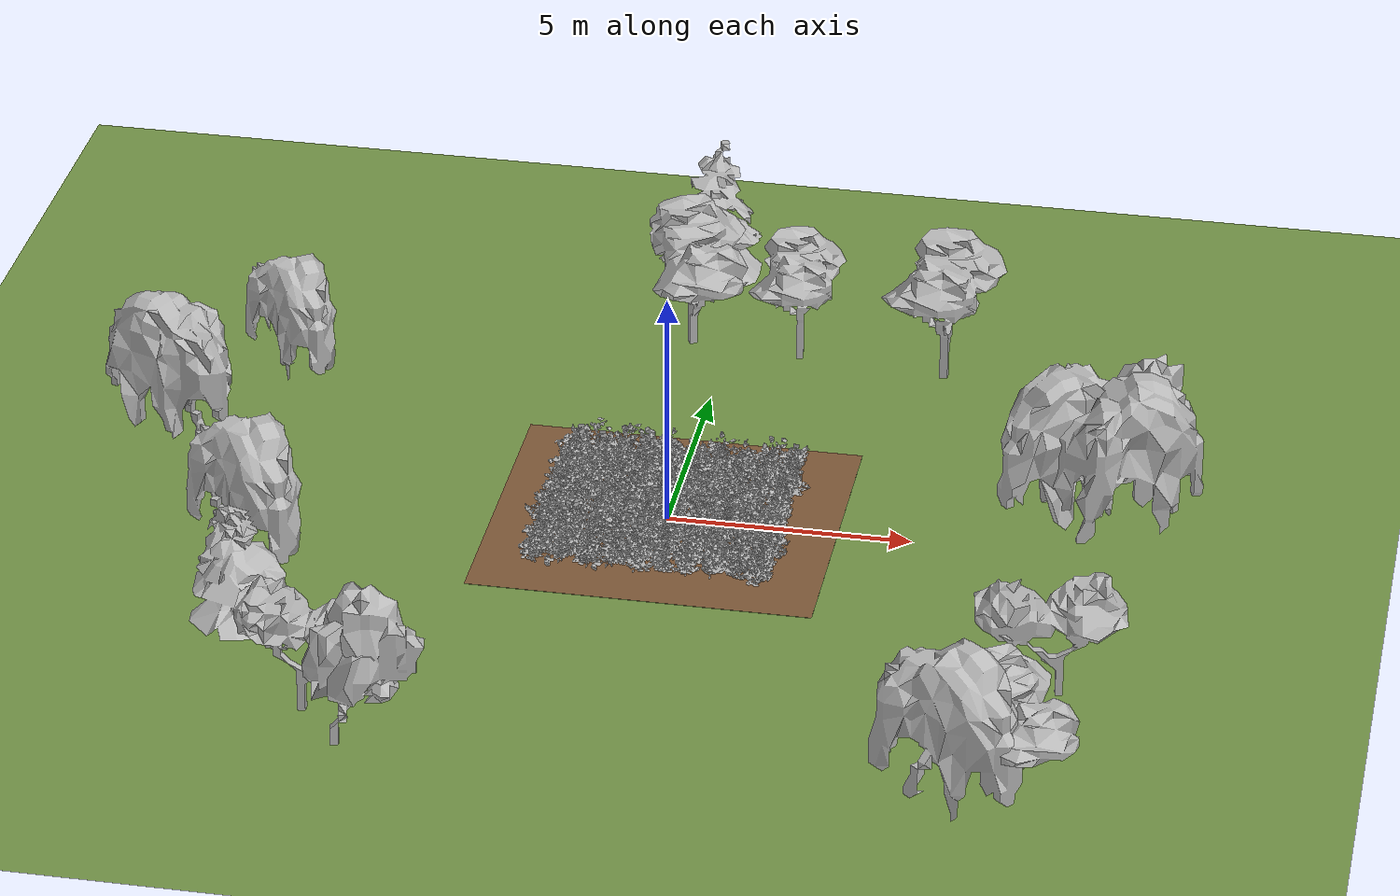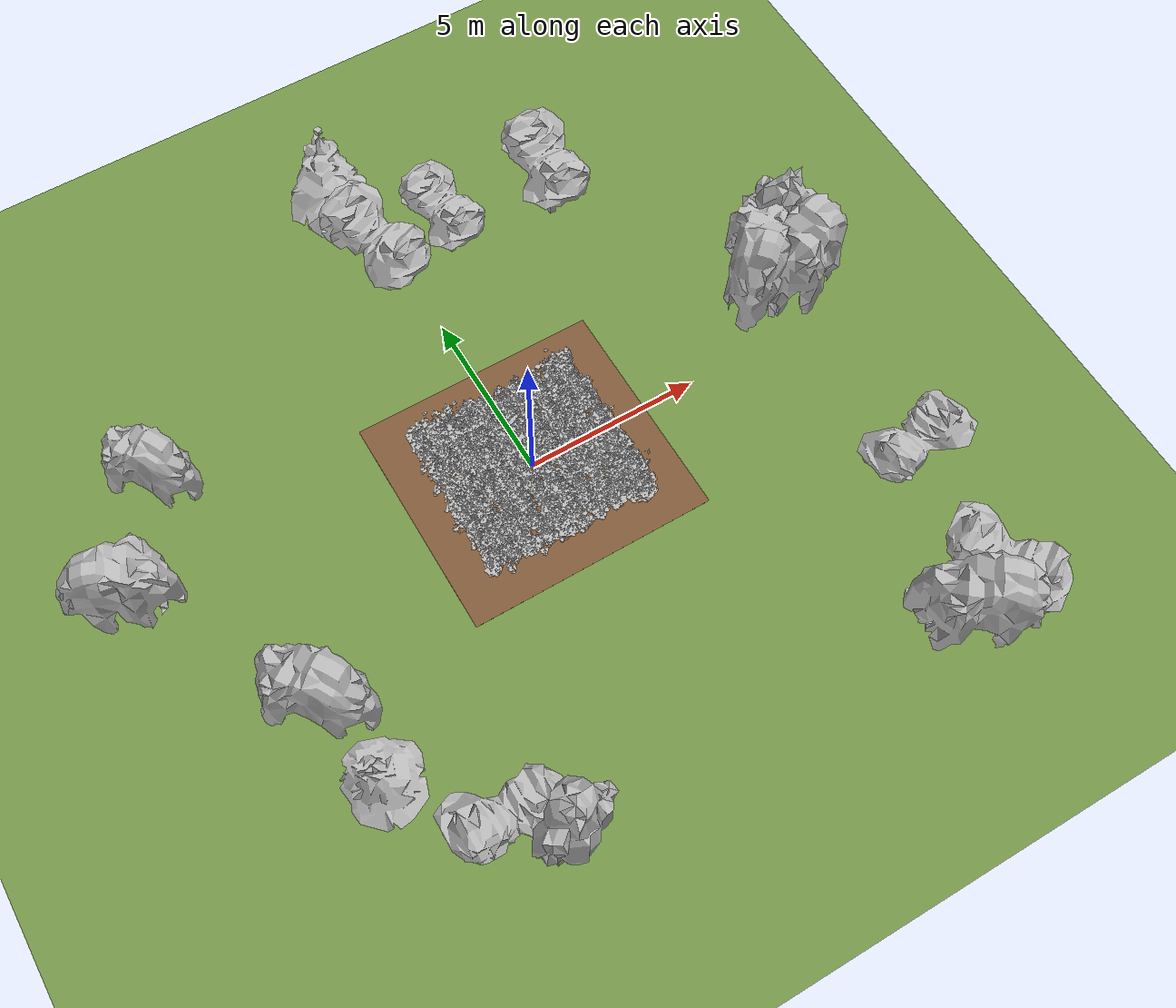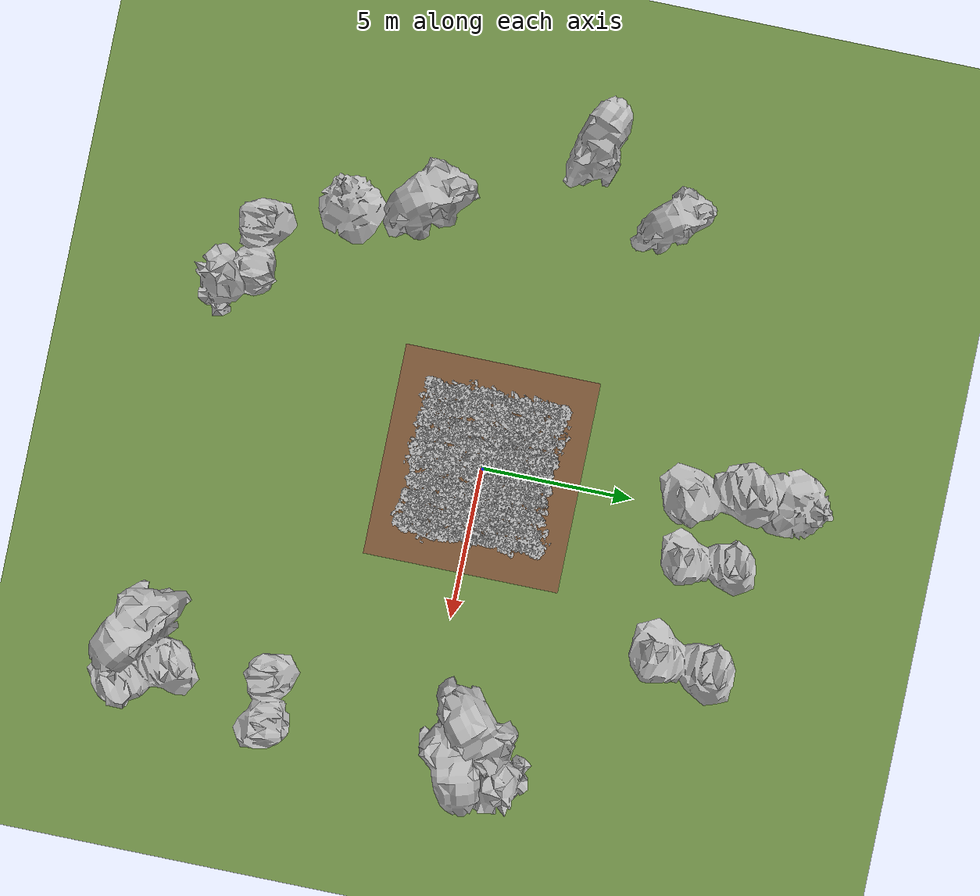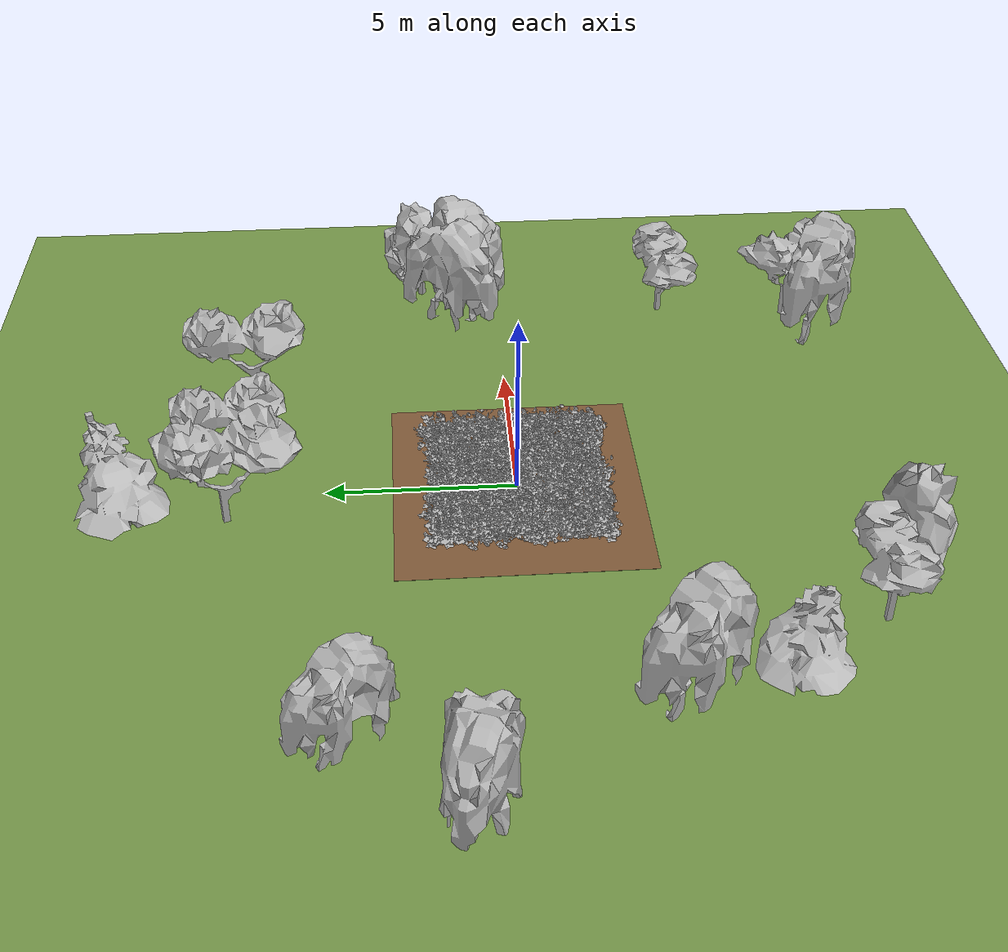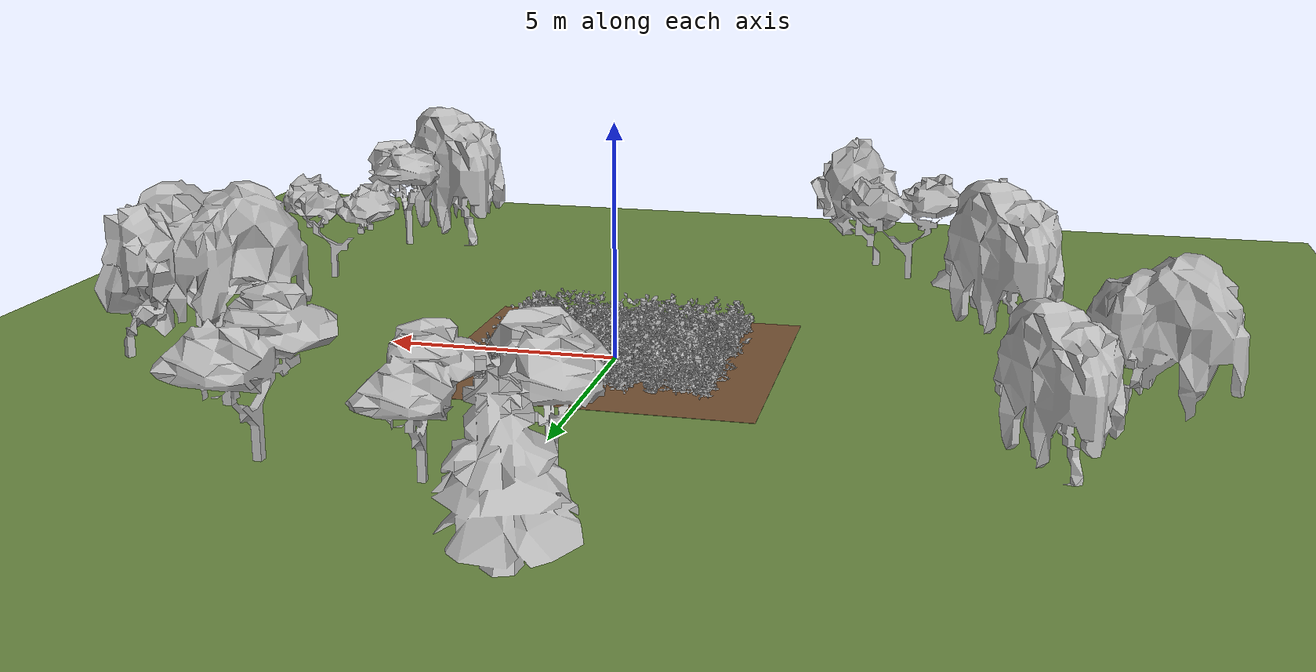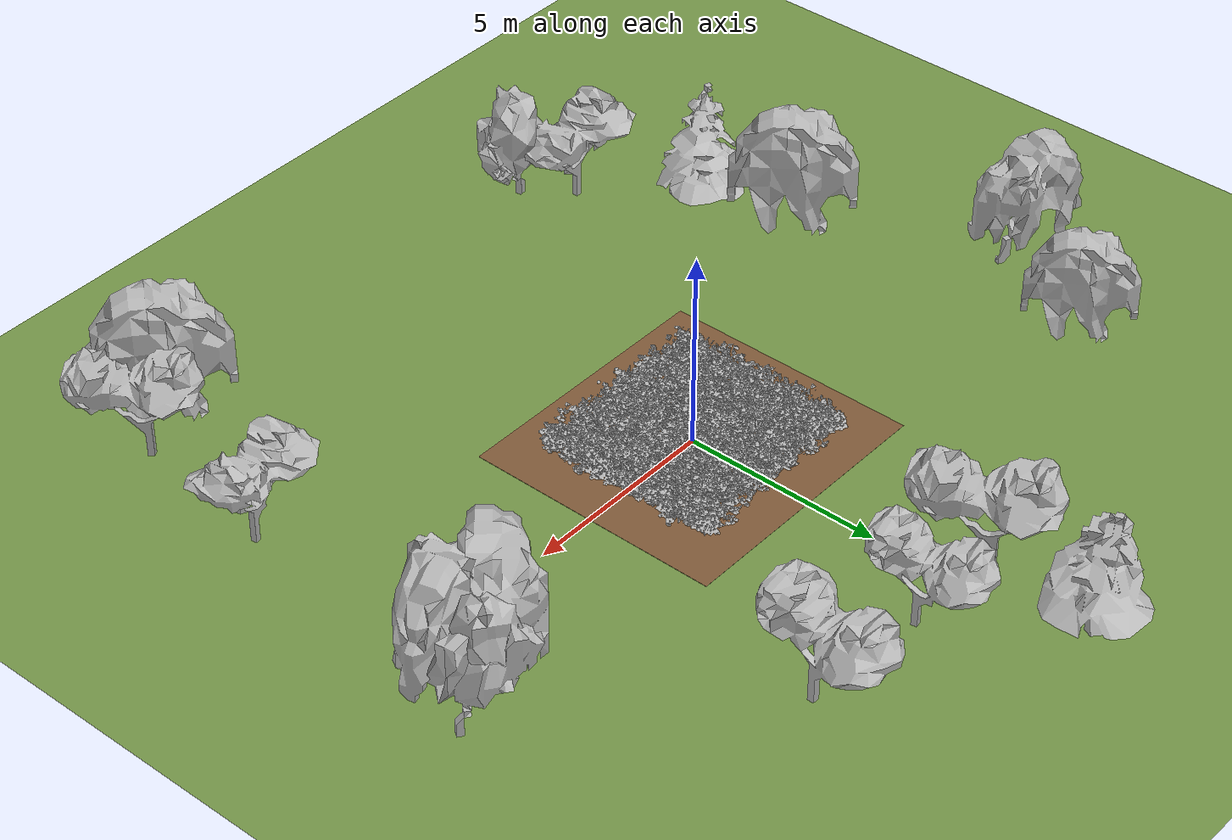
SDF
<?xml version="1.0" ?>
<sdf version="1.9">
  <world name="soybean_farm">

    <physics name="1ms" type="ignored">
      <max_step_size>0.001</max_step_size>
      <real_time_factor>1.0</real_time_factor>
    </physics>

    <plugin filename="gz-sim-physics-system"
            name="gz::sim::systems::Physics"></plugin>
    <plugin filename="gz-sim-user-commands-system"
            name="gz::sim::systems::UserCommands"></plugin>
    <plugin filename="gz-sim-scene-broadcaster-system"
            name="gz::sim::systems::SceneBroadcaster"></plugin>
    <plugin filename="gz-sim-sensors-system"
            name="gz::sim::systems::Sensors">
      <render_engine>ogre2</render_engine>
    </plugin>

    <scene>
      <ambient>0.45 0.47 0.52 1</ambient>
      <background>0.68 0.82 0.93 1</background>
      <shadows>true</shadows>
      <sky></sky>
    </scene>

    <light type="directional" name="sun">
      <cast_shadows>true</cast_shadows>
      <pose>5 5 10 0 0 0</pose>
      <diffuse>1.0 0.98 0.92 1</diffuse>
      <specular>0.4 0.4 0.4 1</specular>
      <direction>-0.5 0.4 -0.85</direction>
      <attenuation>
        <range>1000</range>
        <constant>0.9</constant>
        <linear>0.01</linear>
        <quadratic>0.001</quadratic>
      </attenuation>
    </light>

    <!-- Grass ground (large outer plane) -->
    <model name="grass_ground">
      <static>true</static>
      <link name="link">
        <collision name="collision">
          <geometry>
            <plane>
              <normal>0 0 1</normal>
              <size>40.0 40.0</size>
            </plane>
          </geometry>
        </collision>
        <visual name="visual">
          <geometry>
            <plane>
              <normal>0 0 1</normal>
              <size>40.0 40.0</size>
            </plane>
          </geometry>
          <material>
            <ambient>0.25 0.35 0.18 1</ambient>
            <diffuse>0.45 0.58 0.28 1</diffuse>
            <specular>0.05 0.05 0.05 1</specular>
            <pbr>
              <metal>
                <albedo_map>ground/grass_color_1k.jpg</albedo_map>
                <roughness>0.95</roughness>
                <metalness>0.0</metalness>
              </metal>
            </pbr>
          </material>
        </visual>
      </link>
    </model>

    <!-- Soil field (smaller, on top of grass) -->
    <model name="soil_patch">
      <static>true</static>
      <pose>0 0 0.002 0 0 0</pose>
      <link name="link">
        <visual name="visual">
          <geometry>
            <plane>
              <normal>0 0 1</normal>
              <size>7.00 6.50</size>
            </plane>
          </geometry>
          <material>
            <ambient>0.22 0.15 0.09 1</ambient>
            <diffuse>0.50 0.35 0.22 1</diffuse>
            <specular>0.05 0.05 0.05 1</specular>
            <pbr>
              <metal>
                <albedo_map>ground/soil_color_1k.jpg</albedo_map>
                <roughness>0.95</roughness>
                <metalness>0.0</metalness>
              </metal>
            </pbr>
          </material>
        </visual>
      </link>
    </model>

    <!-- 16 perimeter trees -->
    <model name="tree_00">
      <static>true</static>
      <pose>1.51 7.22 0 1.5708 0 3.29</pose>
      <link name="base_link">
        <visual name="visual">
          <cast_shadows>true</cast_shadows>
          <geometry>
            <mesh>
              <uri>models/tree_common/meshes/tree_common.obj</uri>
              <scale>1.06 1.06 1.06</scale>
            </mesh>
          </geometry>
        </visual>
      </link>
    </model>
    <model name="tree_01">
      <static>true</static>
      <pose>-4.73 -9.23 0 1.5708 0 4.90</pose>
      <link name="base_link">
        <visual name="visual">
          <cast_shadows>true</cast_shadows>
          <geometry>
            <mesh>
              <uri>models/tree_birch/meshes/tree_birch.obj</uri>
              <scale>0.93 0.93 0.93</scale>
            </mesh>
          </geometry>
        </visual>
      </link>
    </model>
    <model name="tree_02">
      <static>true</static>
      <pose>8.62 -5.05 0 1.5708 0 4.88</pose>
      <link name="base_link">
        <visual name="visual">
          <cast_shadows>true</cast_shadows>
          <geometry>
            <mesh>
              <uri>models/tree_common/meshes/tree_common.obj</uri>
              <scale>1.04 1.04 1.04</scale>
            </mesh>
          </geometry>
        </visual>
      </link>
    </model>
    <model name="tree_03">
      <static>true</static>
      <pose>-7.45 -5.83 0 1.5708 0 1.24</pose>
      <link name="base_link">
        <visual name="visual">
          <cast_shadows>true</cast_shadows>
          <geometry>
            <mesh>
              <uri>models/tree_pine/meshes/tree_pine.obj</uri>
              <scale>1.14 1.14 1.14</scale>
            </mesh>
          </geometry>
        </visual>
      </link>
    </model>
    <model name="tree_04">
      <static>true</static>
      <pose>4.64 6.96 0 1.5708 0 3.10</pose>
      <link name="base_link">
        <visual name="visual">
          <cast_shadows>true</cast_shadows>
          <geometry>
            <mesh>
              <uri>models/tree_common/meshes/tree_common.obj</uri>
              <scale>1.20 1.20 1.20</scale>
            </mesh>
          </geometry>
        </visual>
      </link>
    </model>
    <model name="tree_05">
      <static>true</static>
      <pose>6.49 -8.97 0 1.5708 0 4.04</pose>
      <link name="base_link">
        <visual name="visual">
          <cast_shadows>true</cast_shadows>
          <geometry>
            <mesh>
              <uri>models/tree_willow/meshes/tree_willow.obj</uri>
              <scale>1.29 1.29 1.29</scale>
            </mesh>
          </geometry>
        </visual>
      </link>
    </model>
    <model name="tree_06">
      <static>true</static>
      <pose>9.96 2.10 0 1.5708 0 0.95</pose>
      <link name="base_link">
        <visual name="visual">
          <cast_shadows>true</cast_shadows>
          <geometry>
            <mesh>
              <uri>models/tree_birch/meshes/tree_birch.obj</uri>
              <scale>0.93 0.93 0.93</scale>
            </mesh>
          </geometry>
        </visual>
      </link>
    </model>
    <model name="tree_07">
      <static>true</static>
      <pose>-9.03 4.89 0 1.5708 0 3.72</pose>
      <link name="base_link">
        <visual name="visual">
          <cast_shadows>true</cast_shadows>
          <geometry>
            <mesh>
              <uri>models/tree_willow/meshes/tree_willow.obj</uri>
              <scale>1.04 1.04 1.04</scale>
            </mesh>
          </geometry>
        </visual>
      </link>
    </model>
    <model name="tree_08">
      <static>true</static>
      <pose>-0.82 7.49 0 1.5708 0 0.36</pose>
      <link name="base_link">
        <visual name="visual">
          <cast_shadows>true</cast_shadows>
          <geometry>
            <mesh>
              <uri>models/tree_common/meshes/tree_common.obj</uri>
              <scale>1.23 1.23 1.23</scale>
            </mesh>
          </geometry>
        </visual>
      </link>
    </model>
    <model name="tree_09">
      <static>true</static>
      <pose>8.12 -8.83 0 1.5708 0 0.57</pose>
      <link name="base_link">
        <visual name="visual">
          <cast_shadows>true</cast_shadows>
          <geometry>
            <mesh>
              <uri>models/tree_common/meshes/tree_common.obj</uri>
              <scale>1.14 1.14 1.14</scale>
            </mesh>
          </geometry>
        </visual>
      </link>
    </model>
    <model name="tree_10">
      <static>true</static>
      <pose>8.35 0.90 0 1.5708 0 4.98</pose>
      <link name="base_link">
        <visual name="visual">
          <cast_shadows>true</cast_shadows>
          <geometry>
            <mesh>
              <uri>models/tree_willow/meshes/tree_willow.obj</uri>
              <scale>1.26 1.26 1.26</scale>
            </mesh>
          </geometry>
        </visual>
      </link>
    </model>
    <model name="tree_11">
      <static>true</static>
      <pose>-10.14 1.18 0 1.5708 0 1.18</pose>
      <link name="base_link">
        <visual name="visual">
          <cast_shadows>true</cast_shadows>
          <geometry>
            <mesh>
              <uri>models/tree_willow/meshes/tree_willow.obj</uri>
              <scale>1.14 1.14 1.14</scale>
            </mesh>
          </geometry>
        </visual>
      </link>
    </model>
    <model name="tree_12">
      <static>true</static>
      <pose>-0.84 10.08 0 1.5708 0 5.10</pose>
      <link name="base_link">
        <visual name="visual">
          <cast_shadows>true</cast_shadows>
          <geometry>
            <mesh>
              <uri>models/tree_pine/meshes/tree_pine.obj</uri>
              <scale>1.23 1.23 1.23</scale>
            </mesh>
          </geometry>
        </visual>
      </link>
    </model>
    <model name="tree_13">
      <static>true</static>
      <pose>-5.57 -8.27 0 1.5708 0 1.56</pose>
      <link name="base_link">
        <visual name="visual">
          <cast_shadows>true</cast_shadows>
          <geometry>
            <mesh>
              <uri>models/tree_common/meshes/tree_common.obj</uri>
              <scale>1.08 1.08 1.08</scale>
            </mesh>
          </geometry>
        </visual>
      </link>
    </model>
    <model name="tree_14">
      <static>true</static>
      <pose>8.60 1.81 0 1.5708 0 2.29</pose>
      <link name="base_link">
        <visual name="visual">
          <cast_shadows>true</cast_shadows>
          <geometry>
            <mesh>
              <uri>models/tree_willow/meshes/tree_willow.obj</uri>
              <scale>1.27 1.27 1.27</scale>
            </mesh>
          </geometry>
        </visual>
      </link>
    </model>
    <model name="tree_15">
      <static>true</static>
      <pose>-8.14 -2.67 0 1.5708 0 3.76</pose>
      <link name="base_link">
        <visual name="visual">
          <cast_shadows>true</cast_shadows>
          <geometry>
            <mesh>
              <uri>models/tree_willow/meshes/tree_willow.obj</uri>
              <scale>1.22 1.22 1.22</scale>
            </mesh>
          </geometry>
        </visual>
      </link>
    </model>

    <!-- 10 rows x 30 plants = 300 soybean instances -->
    <model name="soybean_000">
      <static>true</static>
      <pose>-2.278 -2.188 0 0 0 1.402</pose>
      <link name="base_link">
        <visual name="visual">
          <cast_shadows>true</cast_shadows>
          <geometry>
            <mesh>
              <uri>models/soybean_plant/meshes/soybean_40d.obj</uri>
            </mesh>
          </geometry>
        </visual>
      </link>
    </model>
    <model name="soybean_001">
      <static>true</static>
      <pose>-2.239 -2.001 0 0 0 0.546</pose>
      <link name="base_link">
        <visual name="visual">
          <cast_shadows>true</cast_shadows>
          <geometry>
            <mesh>
              <uri>models/soybean_plant/meshes/soybean_50d.obj</uri>
            </mesh>
          </geometry>
        </visual>
      </link>
    </model>
    <model name="soybean_002">
      <static>true</static>
      <pose>-2.278 -1.892 0 0 0 3.175</pose>
      <link name="base_link">
        <visual name="visual">
          <cast_shadows>true</cast_shadows>
          <geometry>
            <mesh>
              <uri>models/soybean_plant/meshes/soybean_40d.obj</uri>
            </mesh>
          </geometry>
        </visual>
      </link>
    </model>
    <model name="soybean_003">
      <static>true</static>
      <pose>-2.268 -1.716 0 0 0 3.424</pose>
      <link name="base_link">
        <visual name="visual">
          <cast_shadows>true</cast_shadows>
          <geometry>
            <mesh>
              <uri>models/soybean_plant/meshes/soybean_30d.obj</uri>
            </mesh>
          </geometry>
        </visual>
      </link>
    </model>
    <model name="soybean_004">
      <static>true</static>
      <pose>-2.245 -1.556 0 0 0 0.041</pose>
      <link name="base_link">
        <visual name="visual">
          <cast_shadows>true</cast_shadows>
          <geometry>
            <mesh>
              <uri>models/soybean_plant/meshes/soybean_40d.obj</uri>
            </mesh>
          </geometry>
        </visual>
      </link>
    </model>
    <model name="soybean_005">
      <static>true</static>
      <pose>-2.238 -1.435 0 0 0 0.977</pose>
      <link name="base_link">
        <visual name="visual">
          <cast_shadows>true</cast_shadows>
          <geometry>
            <mesh>
              <uri>models/soybean_plant/meshes/soybean_50d.obj</uri>
            </mesh>
          </geometry>
        </visual>
      </link>
    </model>
    <model name="soybean_006">
      <static>true</static>
      <pose>-2.260 -1.299 0 0 0 0.608</pose>
      <link name="base_link">
        <visual name="visual">
          <cast_shadows>true</cast_shadows>
          <geometry>
            <mesh>
              <uri>models/soybean_plant/meshes/soybean_50d.obj</uri>
            </mesh>
          </geometry>
        </visual>
      </link>
    </model>
    <model name="soybean_007">
      <static>true</static>
      <pose>-2.244 -1.107 0 0 0 4.585</pose>
      <link name="base_link">
        <visual name="visual">
          <cast_shadows>true</cast_shadows>
          <geometry>
            <mesh>
              <uri>models/soybean_plant/meshes/soybean_50d.obj</uri>
            </mesh>
          </geometry>
        </visual>
      </link>
    </model>
    <model name="soybean_008">
      <static>true</static>
      <pose>-2.222 -0.982 0 0 0 3.469</pose>
      <link name="base_link">
        <visual name="visual">
          <cast_shadows>true</cast_shadows>
          <geometry>
            <mesh>
              <uri>models/soybean_plant/meshes/soybean_40d.obj</uri>
            </mesh>
          </geometry>
        </visual>
      </link>
    </model>
    <model name="soybean_009">
      <static>true</static>
      <pose>-2.243 -0.803 0 0 0 3.628</pose>
      <link name="base_link">
        <visual name="visual">
          <cast_shadows>true</cast_shadows>
          <geometry>
            <mesh>
              <uri>models/soybean_plant/meshes/soybean_50d.obj</uri>
            </mesh>
          </geometry>
        </visual>
      </link>
    </model>
    <model name="soybean_010">
      <static>true</static>
      <pose>-2.277 -0.691 0 0 0 1.818</pose>
      <link name="base_link">
        <visual name="visual">
          <cast_shadows>true</cast_shadows>
          <geometry>
            <mesh>
              <uri>models/soybean_plant/meshes/soybean_50d.obj</uri>
            </mesh>
          </geometry>
        </visual>
      </link>
    </model>
    <model name="soybean_011">
      <static>true</static>
      <pose>-2.266 -0.549 0 0 0 1.747</pose>
      <link name="base_link">
        <visual name="visual">
          <cast_shadows>true</cast_shadows>
          <geometry>
            <mesh>
              <uri>models/soybean_plant/meshes/soybean_30d.obj</uri>
            </mesh>
          </geometry>
        </visual>
      </link>
    </model>
    <model name="soybean_012">
      <static>true</static>
      <pose>-2.258 -0.383 0 0 0 1.316</pose>
      <link name="base_link">
        <visual name="visual">
          <cast_shadows>true</cast_shadows>
          <geometry>
            <mesh>
              <uri>models/soybean_plant/meshes/soybean_40d.obj</uri>
            </mesh>
          </geometry>
        </visual>
      </link>
    </model>
    <model name="soybean_013">
      <static>true</static>
      <pose>-2.224 -0.216 0 0 0 3.827</pose>
      <link name="base_link">
        <visual name="visual">
          <cast_shadows>true</cast_shadows>
          <geometry>
            <mesh>
              <uri>models/soybean_plant/meshes/soybean_40d.obj</uri>
            </mesh>
          </geometry>
        </visual>
      </link>
    </model>
    <model name="soybean_014">
      <static>true</static>
      <pose>-2.236 -0.095 0 0 0 2.384</pose>
      <link name="base_link">
        <visual name="visual">
          <cast_shadows>true</cast_shadows>
          <geometry>
            <mesh>
              <uri>models/soybean_plant/meshes/soybean_40d.obj</uri>
            </mesh>
          </geometry>
        </visual>
      </link>
    </model>
    <model name="soybean_015">
      <static>true</static>
      <pose>-2.242 0.078 0 0 0 4.302</pose>
      <link name="base_link">
        <visual name="visual">
          <cast_shadows>true</cast_shadows>
          <geometry>
            <mesh>
              <uri>models/soybean_plant/meshes/soybean_50d.obj</uri>
            </mesh>
          </geometry>
        </visual>
      </link>
    </model>
    <model name="soybean_016">
      <static>true</static>
      <pose>-2.233 0.209 0 0 0 0.202</pose>
      <link name="base_link">
        <visual name="visual">
          <cast_shadows>true</cast_shadows>
          <geometry>
            <mesh>
              <uri>models/soybean_plant/meshes/soybean_50d.obj</uri>
            </mesh>
          </geometry>
        </visual>
      </link>
    </model>
    <model name="soybean_017">
      <static>true</static>
      <pose>-2.264 0.358 0 0 0 5.924</pose>
      <link name="base_link">
        <visual name="visual">
          <cast_shadows>true</cast_shadows>
          <geometry>
            <mesh>
              <uri>models/soybean_plant/meshes/soybean_40d.obj</uri>
            </mesh>
          </geometry>
        </visual>
      </link>
    </model>
    <model name="soybean_018">
      <static>true</static>
      <pose>-2.261 0.534 0 0 0 2.486</pose>
      <link name="base_link">
        <visual name="visual">
          <cast_shadows>true</cast_shadows>
          <geometry>
            <mesh>
              <uri>models/soybean_plant/meshes/soybean_50d.obj</uri>
            </mesh>
          </geometry>
        </visual>
      </link>
    </model>
    <model name="soybean_019">
      <static>true</static>
      <pose>-2.252 0.661 0 0 0 1.550</pose>
      <link name="base_link">
        <visual name="visual">
          <cast_shadows>true</cast_shadows>
          <geometry>
            <mesh>
              <uri>models/soybean_plant/meshes/soybean_50d.obj</uri>
            </mesh>
          </geometry>
        </visual>
      </link>
    </model>
    <model name="soybean_020">
      <static>true</static>
      <pose>-2.264 0.830 0 0 0 5.641</pose>
      <link name="base_link">
        <visual name="visual">
          <cast_shadows>true</cast_shadows>
          <geometry>
            <mesh>
              <uri>models/soybean_plant/meshes/soybean_40d.obj</uri>
            </mesh>
          </geometry>
        </visual>
      </link>
    </model>
    <model name="soybean_021">
      <static>true</static>
      <pose>-2.267 1.005 0 0 0 3.201</pose>
      <link name="base_link">
        <visual name="visual">
          <cast_shadows>true</cast_shadows>
          <geometry>
            <mesh>
              <uri>models/soybean_plant/meshes/soybean_40d.obj</uri>
            </mesh>
          </geometry>
        </visual>
      </link>
    </model>
    <model name="soybean_022">
      <static>true</static>
      <pose>-2.277 1.102 0 0 0 3.942</pose>
      <link name="base_link">
        <visual name="visual">
          <cast_shadows>true</cast_shadows>
          <geometry>
            <mesh>
              <uri>models/soybean_plant/meshes/soybean_30d.obj</uri>
            </mesh>
          </geometry>
        </visual>
      </link>
    </model>
    <model name="soybean_023">
      <static>true</static>
      <pose>-2.255 1.249 0 0 0 2.398</pose>
      <link name="base_link">
        <visual name="visual">
          <cast_shadows>true</cast_shadows>
          <geometry>
            <mesh>
              <uri>models/soybean_plant/meshes/soybean_50d.obj</uri>
            </mesh>
          </geometry>
        </visual>
      </link>
    </model>
    <model name="soybean_024">
      <static>true</static>
      <pose>-2.248 1.453 0 0 0 5.408</pose>
      <link name="base_link">
        <visual name="visual">
          <cast_shadows>true</cast_shadows>
          <geometry>
            <mesh>
              <uri>models/soybean_plant/meshes/soybean_50d.obj</uri>
            </mesh>
          </geometry>
        </visual>
      </link>
    </model>
    <model name="soybean_025">
      <static>true</static>
      <pose>-2.237 1.586 0 0 0 3.374</pose>
      <link name="base_link">
        <visual name="visual">
          <cast_shadows>true</cast_shadows>
          <geometry>
            <mesh>
              <uri>models/soybean_plant/meshes/soybean_30d.obj</uri>
            </mesh>
          </geometry>
        </visual>
      </link>
    </model>
    <model name="soybean_026">
      <static>true</static>
      <pose>-2.242 1.702 0 0 0 2.732</pose>
      <link name="base_link">
        <visual name="visual">
          <cast_shadows>true</cast_shadows>
          <geometry>
            <mesh>
              <uri>models/soybean_plant/meshes/soybean_40d.obj</uri>
            </mesh>
          </geometry>
        </visual>
      </link>
    </model>
    <model name="soybean_027">
      <static>true</static>
      <pose>-2.223 1.898 0 0 0 1.655</pose>
      <link name="base_link">
        <visual name="visual">
          <cast_shadows>true</cast_shadows>
          <geometry>
            <mesh>
              <uri>models/soybean_plant/meshes/soybean_40d.obj</uri>
            </mesh>
          </geometry>
        </visual>
      </link>
    </model>
    <model name="soybean_028">
      <static>true</static>
      <pose>-2.269 2.050 0 0 0 5.470</pose>
      <link name="base_link">
        <visual name="visual">
          <cast_shadows>true</cast_shadows>
          <geometry>
            <mesh>
              <uri>models/soybean_plant/meshes/soybean_40d.obj</uri>
            </mesh>
          </geometry>
        </visual>
      </link>
    </model>
    <model name="soybean_029">
      <static>true</static>
      <pose>-2.242 2.182 0 0 0 0.960</pose>
      <link name="base_link">
        <visual name="visual">
          <cast_shadows>true</cast_shadows>
          <geometry>
            <mesh>
              <uri>models/soybean_plant/meshes/soybean_40d.obj</uri>
            </mesh>
          </geometry>
        </visual>
      </link>
    </model>
    <model name="soybean_030">
      <static>true</static>
      <pose>-1.748 -2.158 0 0 0 3.332</pose>
      <link name="base_link">
        <visual name="visual">
          <cast_shadows>true</cast_shadows>
          <geometry>
            <mesh>
              <uri>models/soybean_plant/meshes/soybean_50d.obj</uri>
            </mesh>
          </geometry>
        </visual>
      </link>
    </model>
    <model name="soybean_031">
      <static>true</static>
      <pose>-1.761 -2.054 0 0 0 5.838</pose>
      <link name="base_link">
        <visual name="visual">
          <cast_shadows>true</cast_shadows>
          <geometry>
            <mesh>
              <uri>models/soybean_plant/meshes/soybean_30d.obj</uri>
            </mesh>
          </geometry>
        </visual>
      </link>
    </model>
    <model name="soybean_032">
      <static>true</static>
      <pose>-1.730 -1.887 0 0 0 0.364</pose>
      <link name="base_link">
        <visual name="visual">
          <cast_shadows>true</cast_shadows>
          <geometry>
            <mesh>
              <uri>models/soybean_plant/meshes/soybean_50d.obj</uri>
            </mesh>
          </geometry>
        </visual>
      </link>
    </model>
    <model name="soybean_033">
      <static>true</static>
      <pose>-1.723 -1.750 0 0 0 3.054</pose>
      <link name="base_link">
        <visual name="visual">
          <cast_shadows>true</cast_shadows>
          <geometry>
            <mesh>
              <uri>models/soybean_plant/meshes/soybean_50d.obj</uri>
            </mesh>
          </geometry>
        </visual>
      </link>
    </model>
    <model name="soybean_034">
      <static>true</static>
      <pose>-1.734 -1.559 0 0 0 0.807</pose>
      <link name="base_link">
        <visual name="visual">
          <cast_shadows>true</cast_shadows>
          <geometry>
            <mesh>
              <uri>models/soybean_plant/meshes/soybean_30d.obj</uri>
            </mesh>
          </geometry>
        </visual>
      </link>
    </model>
    <model name="soybean_035">
      <static>true</static>
      <pose>-1.747 -1.439 0 0 0 5.482</pose>
      <link name="base_link">
        <visual name="visual">
          <cast_shadows>true</cast_shadows>
          <geometry>
            <mesh>
              <uri>models/soybean_plant/meshes/soybean_40d.obj</uri>
            </mesh>
          </geometry>
        </visual>
      </link>
    </model>
    <model name="soybean_036">
      <static>true</static>
      <pose>-1.767 -1.273 0 0 0 4.586</pose>
      <link name="base_link">
        <visual name="visual">
          <cast_shadows>true</cast_shadows>
          <geometry>
            <mesh>
              <uri>models/soybean_plant/meshes/soybean_40d.obj</uri>
            </mesh>
          </geometry>
        </visual>
      </link>
    </model>
    <model name="soybean_037">
      <static>true</static>
      <pose>-1.761 -1.095 0 0 0 4.083</pose>
      <link name="base_link">
        <visual name="visual">
          <cast_shadows>true</cast_shadows>
          <geometry>
            <mesh>
              <uri>models/soybean_plant/meshes/soybean_40d.obj</uri>
            </mesh>
          </geometry>
        </visual>
      </link>
    </model>
    <model name="soybean_038">
      <static>true</static>
      <pose>-1.749 -0.998 0 0 0 1.412</pose>
      <link name="base_link">
        <visual name="visual">
          <cast_shadows>true</cast_shadows>
          <geometry>
            <mesh>
              <uri>models/soybean_plant/meshes/soybean_40d.obj</uri>
            </mesh>
          </geometry>
        </visual>
      </link>
    </model>
    <model name="soybean_039">
      <static>true</static>
      <pose>-1.745 -0.841 0 0 0 1.384</pose>
      <link name="base_link">
        <visual name="visual">
          <cast_shadows>true</cast_shadows>
          <geometry>
            <mesh>
              <uri>models/soybean_plant/meshes/soybean_40d.obj</uri>
            </mesh>
          </geometry>
        </visual>
      </link>
    </model>
    <model name="soybean_040">
      <static>true</static>
      <pose>-1.742 -0.691 0 0 0 5.689</pose>
      <link name="base_link">
        <visual name="visual">
          <cast_shadows>true</cast_shadows>
          <geometry>
            <mesh>
              <uri>models/soybean_plant/meshes/soybean_30d.obj</uri>
            </mesh>
          </geometry>
        </visual>
      </link>
    </model>
    <model name="soybean_041">
      <static>true</static>
      <pose>-1.776 -0.541 0 0 0 4.203</pose>
      <link name="base_link">
        <visual name="visual">
          <cast_shadows>true</cast_shadows>
          <geometry>
            <mesh>
              <uri>models/soybean_plant/meshes/soybean_50d.obj</uri>
            </mesh>
          </geometry>
        </visual>
      </link>
    </model>
    <model name="soybean_042">
      <static>true</static>
      <pose>-1.772 -0.349 0 0 0 3.588</pose>
      <link name="base_link">
        <visual name="visual">
          <cast_shadows>true</cast_shadows>
          <geometry>
            <mesh>
              <uri>models/soybean_plant/meshes/soybean_40d.obj</uri>
            </mesh>
          </geometry>
        </visual>
      </link>
    </model>
    <model name="soybean_043">
      <static>true</static>
      <pose>-1.733 -0.207 0 0 0 1.196</pose>
      <link name="base_link">
        <visual name="visual">
          <cast_shadows>true</cast_shadows>
          <geometry>
            <mesh>
              <uri>models/soybean_plant/meshes/soybean_40d.obj</uri>
            </mesh>
          </geometry>
        </visual>
      </link>
    </model>
    <model name="soybean_044">
      <static>true</static>
      <pose>-1.754 -0.080 0 0 0 2.934</pose>
      <link name="base_link">
        <visual name="visual">
          <cast_shadows>true</cast_shadows>
          <geometry>
            <mesh>
              <uri>models/soybean_plant/meshes/soybean_30d.obj</uri>
            </mesh>
          </geometry>
        </visual>
      </link>
    </model>
    <model name="soybean_045">
      <static>true</static>
      <pose>-1.740 0.104 0 0 0 0.618</pose>
      <link name="base_link">
        <visual name="visual">
          <cast_shadows>true</cast_shadows>
          <geometry>
            <mesh>
              <uri>models/soybean_plant/meshes/soybean_50d.obj</uri>
            </mesh>
          </geometry>
        </visual>
      </link>
    </model>
    <model name="soybean_046">
      <static>true</static>
      <pose>-1.760 0.247 0 0 0 1.562</pose>
      <link name="base_link">
        <visual name="visual">
          <cast_shadows>true</cast_shadows>
          <geometry>
            <mesh>
              <uri>models/soybean_plant/meshes/soybean_40d.obj</uri>
            </mesh>
          </geometry>
        </visual>
      </link>
    </model>
    <model name="soybean_047">
      <static>true</static>
      <pose>-1.753 0.370 0 0 0 1.750</pose>
      <link name="base_link">
        <visual name="visual">
          <cast_shadows>true</cast_shadows>
          <geometry>
            <mesh>
              <uri>models/soybean_plant/meshes/soybean_40d.obj</uri>
            </mesh>
          </geometry>
        </visual>
      </link>
    </model>
    <model name="soybean_048">
      <static>true</static>
      <pose>-1.725 0.522 0 0 0 5.412</pose>
      <link name="base_link">
        <visual name="visual">
          <cast_shadows>true</cast_shadows>
          <geometry>
            <mesh>
              <uri>models/soybean_plant/meshes/soybean_40d.obj</uri>
            </mesh>
          </geometry>
        </visual>
      </link>
    </model>
    <model name="soybean_049">
      <static>true</static>
      <pose>-1.777 0.705 0 0 0 5.253</pose>
      <link name="base_link">
        <visual name="visual">
          <cast_shadows>true</cast_shadows>
          <geometry>
            <mesh>
              <uri>models/soybean_plant/meshes/soybean_40d.obj</uri>
            </mesh>
          </geometry>
        </visual>
      </link>
    </model>
    <model name="soybean_050">
      <static>true</static>
      <pose>-1.724 0.846 0 0 0 1.045</pose>
      <link name="base_link">
        <visual name="visual">
          <cast_shadows>true</cast_shadows>
          <geometry>
            <mesh>
              <uri>models/soybean_plant/meshes/soybean_50d.obj</uri>
            </mesh>
          </geometry>
        </visual>
      </link>
    </model>
    <model name="soybean_051">
      <static>true</static>
      <pose>-1.767 0.969 0 0 0 0.368</pose>
      <link name="base_link">
        <visual name="visual">
          <cast_shadows>true</cast_shadows>
          <geometry>
            <mesh>
              <uri>models/soybean_plant/meshes/soybean_40d.obj</uri>
            </mesh>
          </geometry>
        </visual>
      </link>
    </model>
    <model name="soybean_052">
      <static>true</static>
      <pose>-1.721 1.111 0 0 0 4.926</pose>
      <link name="base_link">
        <visual name="visual">
          <cast_shadows>true</cast_shadows>
          <geometry>
            <mesh>
              <uri>models/soybean_plant/meshes/soybean_40d.obj</uri>
            </mesh>
          </geometry>
        </visual>
      </link>
    </model>
    <model name="soybean_053">
      <static>true</static>
      <pose>-1.755 1.302 0 0 0 6.254</pose>
      <link name="base_link">
        <visual name="visual">
          <cast_shadows>true</cast_shadows>
          <geometry>
            <mesh>
              <uri>models/soybean_plant/meshes/soybean_40d.obj</uri>
            </mesh>
          </geometry>
        </visual>
      </link>
    </model>
    <model name="soybean_054">
      <static>true</static>
      <pose>-1.737 1.404 0 0 0 1.864</pose>
      <link name="base_link">
        <visual name="visual">
          <cast_shadows>true</cast_shadows>
          <geometry>
            <mesh>
              <uri>models/soybean_plant/meshes/soybean_40d.obj</uri>
            </mesh>
          </geometry>
        </visual>
      </link>
    </model>
    <model name="soybean_055">
      <static>true</static>
      <pose>-1.745 1.578 0 0 0 4.700</pose>
      <link name="base_link">
        <visual name="visual">
          <cast_shadows>true</cast_shadows>
          <geometry>
            <mesh>
              <uri>models/soybean_plant/meshes/soybean_50d.obj</uri>
            </mesh>
          </geometry>
        </visual>
      </link>
    </model>
    <model name="soybean_056">
      <static>true</static>
      <pose>-1.745 1.725 0 0 0 5.358</pose>
      <link name="base_link">
        <visual name="visual">
          <cast_shadows>true</cast_shadows>
          <geometry>
            <mesh>
              <uri>models/soybean_plant/meshes/soybean_30d.obj</uri>
            </mesh>
          </geometry>
        </visual>
      </link>
    </model>
    <model name="soybean_057">
      <static>true</static>
      <pose>-1.722 1.850 0 0 0 1.168</pose>
      <link name="base_link">
        <visual name="visual">
          <cast_shadows>true</cast_shadows>
          <geometry>
            <mesh>
              <uri>models/soybean_plant/meshes/soybean_40d.obj</uri>
            </mesh>
          </geometry>
        </visual>
      </link>
    </model>
    <model name="soybean_058">
      <static>true</static>
      <pose>-1.739 2.009 0 0 0 0.753</pose>
      <link name="base_link">
        <visual name="visual">
          <cast_shadows>true</cast_shadows>
          <geometry>
            <mesh>
              <uri>models/soybean_plant/meshes/soybean_40d.obj</uri>
            </mesh>
          </geometry>
        </visual>
      </link>
    </model>
    <model name="soybean_059">
      <static>true</static>
      <pose>-1.765 2.181 0 0 0 3.892</pose>
      <link name="base_link">
        <visual name="visual">
          <cast_shadows>true</cast_shadows>
          <geometry>
            <mesh>
              <uri>models/soybean_plant/meshes/soybean_50d.obj</uri>
            </mesh>
          </geometry>
        </visual>
      </link>
    </model>
    <model name="soybean_060">
      <static>true</static>
      <pose>-1.245 -2.174 0 0 0 5.873</pose>
      <link name="base_link">
        <visual name="visual">
          <cast_shadows>true</cast_shadows>
          <geometry>
            <mesh>
              <uri>models/soybean_plant/meshes/soybean_40d.obj</uri>
            </mesh>
          </geometry>
        </visual>
      </link>
    </model>
    <model name="soybean_061">
      <static>true</static>
      <pose>-1.237 -2.041 0 0 0 2.487</pose>
      <link name="base_link">
        <visual name="visual">
          <cast_shadows>true</cast_shadows>
          <geometry>
            <mesh>
              <uri>models/soybean_plant/meshes/soybean_40d.obj</uri>
            </mesh>
          </geometry>
        </visual>
      </link>
    </model>
    <model name="soybean_062">
      <static>true</static>
      <pose>-1.262 -1.886 0 0 0 4.724</pose>
      <link name="base_link">
        <visual name="visual">
          <cast_shadows>true</cast_shadows>
          <geometry>
            <mesh>
              <uri>models/soybean_plant/meshes/soybean_50d.obj</uri>
            </mesh>
          </geometry>
        </visual>
      </link>
    </model>
    <model name="soybean_063">
      <static>true</static>
      <pose>-1.253 -1.695 0 0 0 6.259</pose>
      <link name="base_link">
        <visual name="visual">
          <cast_shadows>true</cast_shadows>
          <geometry>
            <mesh>
              <uri>models/soybean_plant/meshes/soybean_30d.obj</uri>
            </mesh>
          </geometry>
        </visual>
      </link>
    </model>
    <model name="soybean_064">
      <static>true</static>
      <pose>-1.267 -1.589 0 0 0 5.864</pose>
      <link name="base_link">
        <visual name="visual">
          <cast_shadows>true</cast_shadows>
          <geometry>
            <mesh>
              <uri>models/soybean_plant/meshes/soybean_30d.obj</uri>
            </mesh>
          </geometry>
        </visual>
      </link>
    </model>
    <model name="soybean_065">
      <static>true</static>
      <pose>-1.227 -1.433 0 0 0 0.991</pose>
      <link name="base_link">
        <visual name="visual">
          <cast_shadows>true</cast_shadows>
          <geometry>
            <mesh>
              <uri>models/soybean_plant/meshes/soybean_50d.obj</uri>
            </mesh>
          </geometry>
        </visual>
      </link>
    </model>
    <model name="soybean_066">
      <static>true</static>
      <pose>-1.238 -1.268 0 0 0 6.203</pose>
      <link name="base_link">
        <visual name="visual">
          <cast_shadows>true</cast_shadows>
          <geometry>
            <mesh>
              <uri>models/soybean_plant/meshes/soybean_50d.obj</uri>
            </mesh>
          </geometry>
        </visual>
      </link>
    </model>
    <model name="soybean_067">
      <static>true</static>
      <pose>-1.280 -1.106 0 0 0 1.881</pose>
      <link name="base_link">
        <visual name="visual">
          <cast_shadows>true</cast_shadows>
          <geometry>
            <mesh>
              <uri>models/soybean_plant/meshes/soybean_50d.obj</uri>
            </mesh>
          </geometry>
        </visual>
      </link>
    </model>
    <model name="soybean_068">
      <static>true</static>
      <pose>-1.224 -0.997 0 0 0 0.725</pose>
      <link name="base_link">
        <visual name="visual">
          <cast_shadows>true</cast_shadows>
          <geometry>
            <mesh>
              <uri>models/soybean_plant/meshes/soybean_50d.obj</uri>
            </mesh>
          </geometry>
        </visual>
      </link>
    </model>
    <model name="soybean_069">
      <static>true</static>
      <pose>-1.247 -0.839 0 0 0 3.800</pose>
      <link name="base_link">
        <visual name="visual">
          <cast_shadows>true</cast_shadows>
          <geometry>
            <mesh>
              <uri>models/soybean_plant/meshes/soybean_30d.obj</uri>
            </mesh>
          </geometry>
        </visual>
      </link>
    </model>
    <model name="soybean_070">
      <static>true</static>
      <pose>-1.268 -0.667 0 0 0 1.659</pose>
      <link name="base_link">
        <visual name="visual">
          <cast_shadows>true</cast_shadows>
          <geometry>
            <mesh>
              <uri>models/soybean_plant/meshes/soybean_50d.obj</uri>
            </mesh>
          </geometry>
        </visual>
      </link>
    </model>
    <model name="soybean_071">
      <static>true</static>
      <pose>-1.226 -0.504 0 0 0 0.580</pose>
      <link name="base_link">
        <visual name="visual">
          <cast_shadows>true</cast_shadows>
          <geometry>
            <mesh>
              <uri>models/soybean_plant/meshes/soybean_40d.obj</uri>
            </mesh>
          </geometry>
        </visual>
      </link>
    </model>
    <model name="soybean_072">
      <static>true</static>
      <pose>-1.263 -0.405 0 0 0 4.845</pose>
      <link name="base_link">
        <visual name="visual">
          <cast_shadows>true</cast_shadows>
          <geometry>
            <mesh>
              <uri>models/soybean_plant/meshes/soybean_40d.obj</uri>
            </mesh>
          </geometry>
        </visual>
      </link>
    </model>
    <model name="soybean_073">
      <static>true</static>
      <pose>-1.264 -0.211 0 0 0 3.466</pose>
      <link name="base_link">
        <visual name="visual">
          <cast_shadows>true</cast_shadows>
          <geometry>
            <mesh>
              <uri>models/soybean_plant/meshes/soybean_40d.obj</uri>
            </mesh>
          </geometry>
        </visual>
      </link>
    </model>
    <model name="soybean_074">
      <static>true</static>
      <pose>-1.279 -0.100 0 0 0 5.549</pose>
      <link name="base_link">
        <visual name="visual">
          <cast_shadows>true</cast_shadows>
          <geometry>
            <mesh>
              <uri>models/soybean_plant/meshes/soybean_40d.obj</uri>
            </mesh>
          </geometry>
        </visual>
      </link>
    </model>
    <model name="soybean_075">
      <static>true</static>
      <pose>-1.247 0.095 0 0 0 3.660</pose>
      <link name="base_link">
        <visual name="visual">
          <cast_shadows>true</cast_shadows>
          <geometry>
            <mesh>
              <uri>models/soybean_plant/meshes/soybean_50d.obj</uri>
            </mesh>
          </geometry>
        </visual>
      </link>
    </model>
    <model name="soybean_076">
      <static>true</static>
      <pose>-1.272 0.213 0 0 0 5.648</pose>
      <link name="base_link">
        <visual name="visual">
          <cast_shadows>true</cast_shadows>
          <geometry>
            <mesh>
              <uri>models/soybean_plant/meshes/soybean_30d.obj</uri>
            </mesh>
          </geometry>
        </visual>
      </link>
    </model>
    <model name="soybean_077">
      <static>true</static>
      <pose>-1.228 0.399 0 0 0 1.320</pose>
      <link name="base_link">
        <visual name="visual">
          <cast_shadows>true</cast_shadows>
          <geometry>
            <mesh>
              <uri>models/soybean_plant/meshes/soybean_50d.obj</uri>
            </mesh>
          </geometry>
        </visual>
      </link>
    </model>
    <model name="soybean_078">
      <static>true</static>
      <pose>-1.274 0.542 0 0 0 5.555</pose>
      <link name="base_link">
        <visual name="visual">
          <cast_shadows>true</cast_shadows>
          <geometry>
            <mesh>
              <uri>models/soybean_plant/meshes/soybean_40d.obj</uri>
            </mesh>
          </geometry>
        </visual>
      </link>
    </model>
    <model name="soybean_079">
      <static>true</static>
      <pose>-1.243 0.654 0 0 0 5.843</pose>
      <link name="base_link">
        <visual name="visual">
          <cast_shadows>true</cast_shadows>
          <geometry>
            <mesh>
              <uri>models/soybean_plant/meshes/soybean_40d.obj</uri>
            </mesh>
          </geometry>
        </visual>
      </link>
    </model>
    <model name="soybean_080">
      <static>true</static>
      <pose>-1.221 0.844 0 0 0 5.538</pose>
      <link name="base_link">
        <visual name="visual">
          <cast_shadows>true</cast_shadows>
          <geometry>
            <mesh>
              <uri>models/soybean_plant/meshes/soybean_50d.obj</uri>
            </mesh>
          </geometry>
        </visual>
      </link>
    </model>
    <model name="soybean_081">
      <static>true</static>
      <pose>-1.236 0.965 0 0 0 5.849</pose>
      <link name="base_link">
        <visual name="visual">
          <cast_shadows>true</cast_shadows>
          <geometry>
            <mesh>
              <uri>models/soybean_plant/meshes/soybean_30d.obj</uri>
            </mesh>
          </geometry>
        </visual>
      </link>
    </model>
    <model name="soybean_082">
      <static>true</static>
      <pose>-1.228 1.144 0 0 0 1.676</pose>
      <link name="base_link">
        <visual name="visual">
          <cast_shadows>true</cast_shadows>
          <geometry>
            <mesh>
              <uri>models/soybean_plant/meshes/soybean_50d.obj</uri>
            </mesh>
          </geometry>
        </visual>
      </link>
    </model>
    <model name="soybean_083">
      <static>true</static>
      <pose>-1.274 1.297 0 0 0 5.395</pose>
      <link name="base_link">
        <visual name="visual">
          <cast_shadows>true</cast_shadows>
          <geometry>
            <mesh>
              <uri>models/soybean_plant/meshes/soybean_50d.obj</uri>
            </mesh>
          </geometry>
        </visual>
      </link>
    </model>
    <model name="soybean_084">
      <static>true</static>
      <pose>-1.231 1.423 0 0 0 1.918</pose>
      <link name="base_link">
        <visual name="visual">
          <cast_shadows>true</cast_shadows>
          <geometry>
            <mesh>
              <uri>models/soybean_plant/meshes/soybean_40d.obj</uri>
            </mesh>
          </geometry>
        </visual>
      </link>
    </model>
    <model name="soybean_085">
      <static>true</static>
      <pose>-1.266 1.546 0 0 0 1.213</pose>
      <link name="base_link">
        <visual name="visual">
          <cast_shadows>true</cast_shadows>
          <geometry>
            <mesh>
              <uri>models/soybean_plant/meshes/soybean_50d.obj</uri>
            </mesh>
          </geometry>
        </visual>
      </link>
    </model>
    <model name="soybean_086">
      <static>true</static>
      <pose>-1.228 1.753 0 0 0 1.754</pose>
      <link name="base_link">
        <visual name="visual">
          <cast_shadows>true</cast_shadows>
          <geometry>
            <mesh>
              <uri>models/soybean_plant/meshes/soybean_40d.obj</uri>
            </mesh>
          </geometry>
        </visual>
      </link>
    </model>
    <model name="soybean_087">
      <static>true</static>
      <pose>-1.256 1.904 0 0 0 3.369</pose>
      <link name="base_link">
        <visual name="visual">
          <cast_shadows>true</cast_shadows>
          <geometry>
            <mesh>
              <uri>models/soybean_plant/meshes/soybean_40d.obj</uri>
            </mesh>
          </geometry>
        </visual>
      </link>
    </model>
    <model name="soybean_088">
      <static>true</static>
      <pose>-1.273 2.053 0 0 0 1.122</pose>
      <link name="base_link">
        <visual name="visual">
          <cast_shadows>true</cast_shadows>
          <geometry>
            <mesh>
              <uri>models/soybean_plant/meshes/soybean_50d.obj</uri>
            </mesh>
          </geometry>
        </visual>
      </link>
    </model>
    <model name="soybean_089">
      <static>true</static>
      <pose>-1.264 2.152 0 0 0 2.730</pose>
      <link name="base_link">
        <visual name="visual">
          <cast_shadows>true</cast_shadows>
          <geometry>
            <mesh>
              <uri>models/soybean_plant/meshes/soybean_50d.obj</uri>
            </mesh>
          </geometry>
        </visual>
      </link>
    </model>
    <model name="soybean_090">
      <static>true</static>
      <pose>-0.761 -2.169 0 0 0 3.213</pose>
      <link name="base_link">
        <visual name="visual">
          <cast_shadows>true</cast_shadows>
          <geometry>
            <mesh>
              <uri>models/soybean_plant/meshes/soybean_50d.obj</uri>
            </mesh>
          </geometry>
        </visual>
      </link>
    </model>
    <model name="soybean_091">
      <static>true</static>
      <pose>-0.745 -2.040 0 0 0 4.453</pose>
      <link name="base_link">
        <visual name="visual">
          <cast_shadows>true</cast_shadows>
          <geometry>
            <mesh>
              <uri>models/soybean_plant/meshes/soybean_40d.obj</uri>
            </mesh>
          </geometry>
        </visual>
      </link>
    </model>
    <model name="soybean_092">
      <static>true</static>
      <pose>-0.724 -1.873 0 0 0 4.520</pose>
      <link name="base_link">
        <visual name="visual">
          <cast_shadows>true</cast_shadows>
          <geometry>
            <mesh>
              <uri>models/soybean_plant/meshes/soybean_30d.obj</uri>
            </mesh>
          </geometry>
        </visual>
      </link>
    </model>
    <model name="soybean_093">
      <static>true</static>
      <pose>-0.740 -1.733 0 0 0 0.440</pose>
      <link name="base_link">
        <visual name="visual">
          <cast_shadows>true</cast_shadows>
          <geometry>
            <mesh>
              <uri>models/soybean_plant/meshes/soybean_50d.obj</uri>
            </mesh>
          </geometry>
        </visual>
      </link>
    </model>
    <model name="soybean_094">
      <static>true</static>
      <pose>-0.760 -1.586 0 0 0 5.328</pose>
      <link name="base_link">
        <visual name="visual">
          <cast_shadows>true</cast_shadows>
          <geometry>
            <mesh>
              <uri>models/soybean_plant/meshes/soybean_50d.obj</uri>
            </mesh>
          </geometry>
        </visual>
      </link>
    </model>
    <model name="soybean_095">
      <static>true</static>
      <pose>-0.762 -1.436 0 0 0 2.566</pose>
      <link name="base_link">
        <visual name="visual">
          <cast_shadows>true</cast_shadows>
          <geometry>
            <mesh>
              <uri>models/soybean_plant/meshes/soybean_50d.obj</uri>
            </mesh>
          </geometry>
        </visual>
      </link>
    </model>
    <model name="soybean_096">
      <static>true</static>
      <pose>-0.762 -1.297 0 0 0 2.642</pose>
      <link name="base_link">
        <visual name="visual">
          <cast_shadows>true</cast_shadows>
          <geometry>
            <mesh>
              <uri>models/soybean_plant/meshes/soybean_40d.obj</uri>
            </mesh>
          </geometry>
        </visual>
      </link>
    </model>
    <model name="soybean_097">
      <static>true</static>
      <pose>-0.739 -1.101 0 0 0 3.867</pose>
      <link name="base_link">
        <visual name="visual">
          <cast_shadows>true</cast_shadows>
          <geometry>
            <mesh>
              <uri>models/soybean_plant/meshes/soybean_50d.obj</uri>
            </mesh>
          </geometry>
        </visual>
      </link>
    </model>
    <model name="soybean_098">
      <static>true</static>
      <pose>-0.747 -1.005 0 0 0 1.803</pose>
      <link name="base_link">
        <visual name="visual">
          <cast_shadows>true</cast_shadows>
          <geometry>
            <mesh>
              <uri>models/soybean_plant/meshes/soybean_40d.obj</uri>
            </mesh>
          </geometry>
        </visual>
      </link>
    </model>
    <model name="soybean_099">
      <static>true</static>
      <pose>-0.745 -0.816 0 0 0 2.922</pose>
      <link name="base_link">
        <visual name="visual">
          <cast_shadows>true</cast_shadows>
          <geometry>
            <mesh>
              <uri>models/soybean_plant/meshes/soybean_40d.obj</uri>
            </mesh>
          </geometry>
        </visual>
      </link>
    </model>
    <model name="soybean_100">
      <static>true</static>
      <pose>-0.767 -0.677 0 0 0 5.662</pose>
      <link name="base_link">
        <visual name="visual">
          <cast_shadows>true</cast_shadows>
          <geometry>
            <mesh>
              <uri>models/soybean_plant/meshes/soybean_40d.obj</uri>
            </mesh>
          </geometry>
        </visual>
      </link>
    </model>
    <model name="soybean_101">
      <static>true</static>
      <pose>-0.770 -0.550 0 0 0 3.239</pose>
      <link name="base_link">
        <visual name="visual">
          <cast_shadows>true</cast_shadows>
          <geometry>
            <mesh>
              <uri>models/soybean_plant/meshes/soybean_50d.obj</uri>
            </mesh>
          </geometry>
        </visual>
      </link>
    </model>
    <model name="soybean_102">
      <static>true</static>
      <pose>-0.760 -0.356 0 0 0 4.720</pose>
      <link name="base_link">
        <visual name="visual">
          <cast_shadows>true</cast_shadows>
          <geometry>
            <mesh>
              <uri>models/soybean_plant/meshes/soybean_40d.obj</uri>
            </mesh>
          </geometry>
        </visual>
      </link>
    </model>
    <model name="soybean_103">
      <static>true</static>
      <pose>-0.767 -0.243 0 0 0 0.153</pose>
      <link name="base_link">
        <visual name="visual">
          <cast_shadows>true</cast_shadows>
          <geometry>
            <mesh>
              <uri>models/soybean_plant/meshes/soybean_50d.obj</uri>
            </mesh>
          </geometry>
        </visual>
      </link>
    </model>
    <model name="soybean_104">
      <static>true</static>
      <pose>-0.751 -0.054 0 0 0 0.458</pose>
      <link name="base_link">
        <visual name="visual">
          <cast_shadows>true</cast_shadows>
          <geometry>
            <mesh>
              <uri>models/soybean_plant/meshes/soybean_40d.obj</uri>
            </mesh>
          </geometry>
        </visual>
      </link>
    </model>
    <model name="soybean_105">
      <static>true</static>
      <pose>-0.742 0.057 0 0 0 4.375</pose>
      <link name="base_link">
        <visual name="visual">
          <cast_shadows>true</cast_shadows>
          <geometry>
            <mesh>
              <uri>models/soybean_plant/meshes/soybean_40d.obj</uri>
            </mesh>
          </geometry>
        </visual>
      </link>
    </model>
    <model name="soybean_106">
      <static>true</static>
      <pose>-0.765 0.234 0 0 0 0.035</pose>
      <link name="base_link">
        <visual name="visual">
          <cast_shadows>true</cast_shadows>
          <geometry>
            <mesh>
              <uri>models/soybean_plant/meshes/soybean_40d.obj</uri>
            </mesh>
          </geometry>
        </visual>
      </link>
    </model>
    <model name="soybean_107">
      <static>true</static>
      <pose>-0.734 0.351 0 0 0 2.671</pose>
      <link name="base_link">
        <visual name="visual">
          <cast_shadows>true</cast_shadows>
          <geometry>
            <mesh>
              <uri>models/soybean_plant/meshes/soybean_50d.obj</uri>
            </mesh>
          </geometry>
        </visual>
      </link>
    </model>
    <model name="soybean_108">
      <static>true</static>
      <pose>-0.723 0.526 0 0 0 0.316</pose>
      <link name="base_link">
        <visual name="visual">
          <cast_shadows>true</cast_shadows>
          <geometry>
            <mesh>
              <uri>models/soybean_plant/meshes/soybean_40d.obj</uri>
            </mesh>
          </geometry>
        </visual>
      </link>
    </model>
    <model name="soybean_109">
      <static>true</static>
      <pose>-0.729 0.672 0 0 0 5.035</pose>
      <link name="base_link">
        <visual name="visual">
          <cast_shadows>true</cast_shadows>
          <geometry>
            <mesh>
              <uri>models/soybean_plant/meshes/soybean_40d.obj</uri>
            </mesh>
          </geometry>
        </visual>
      </link>
    </model>
    <model name="soybean_110">
      <static>true</static>
      <pose>-0.721 0.831 0 0 0 5.969</pose>
      <link name="base_link">
        <visual name="visual">
          <cast_shadows>true</cast_shadows>
          <geometry>
            <mesh>
              <uri>models/soybean_plant/meshes/soybean_50d.obj</uri>
            </mesh>
          </geometry>
        </visual>
      </link>
    </model>
    <model name="soybean_111">
      <static>true</static>
      <pose>-0.743 0.988 0 0 0 3.172</pose>
      <link name="base_link">
        <visual name="visual">
          <cast_shadows>true</cast_shadows>
          <geometry>
            <mesh>
              <uri>models/soybean_plant/meshes/soybean_50d.obj</uri>
            </mesh>
          </geometry>
        </visual>
      </link>
    </model>
    <model name="soybean_112">
      <static>true</static>
      <pose>-0.747 1.149 0 0 0 4.673</pose>
      <link name="base_link">
        <visual name="visual">
          <cast_shadows>true</cast_shadows>
          <geometry>
            <mesh>
              <uri>models/soybean_plant/meshes/soybean_50d.obj</uri>
            </mesh>
          </geometry>
        </visual>
      </link>
    </model>
    <model name="soybean_113">
      <static>true</static>
      <pose>-0.764 1.260 0 0 0 4.007</pose>
      <link name="base_link">
        <visual name="visual">
          <cast_shadows>true</cast_shadows>
          <geometry>
            <mesh>
              <uri>models/soybean_plant/meshes/soybean_40d.obj</uri>
            </mesh>
          </geometry>
        </visual>
      </link>
    </model>
    <model name="soybean_114">
      <static>true</static>
      <pose>-0.749 1.433 0 0 0 1.725</pose>
      <link name="base_link">
        <visual name="visual">
          <cast_shadows>true</cast_shadows>
          <geometry>
            <mesh>
              <uri>models/soybean_plant/meshes/soybean_50d.obj</uri>
            </mesh>
          </geometry>
        </visual>
      </link>
    </model>
    <model name="soybean_115">
      <static>true</static>
      <pose>-0.763 1.561 0 0 0 2.009</pose>
      <link name="base_link">
        <visual name="visual">
          <cast_shadows>true</cast_shadows>
          <geometry>
            <mesh>
              <uri>models/soybean_plant/meshes/soybean_30d.obj</uri>
            </mesh>
          </geometry>
        </visual>
      </link>
    </model>
    <model name="soybean_116">
      <static>true</static>
      <pose>-0.772 1.709 0 0 0 4.360</pose>
      <link name="base_link">
        <visual name="visual">
          <cast_shadows>true</cast_shadows>
          <geometry>
            <mesh>
              <uri>models/soybean_plant/meshes/soybean_40d.obj</uri>
            </mesh>
          </geometry>
        </visual>
      </link>
    </model>
    <model name="soybean_117">
      <static>true</static>
      <pose>-0.776 1.869 0 0 0 3.409</pose>
      <link name="base_link">
        <visual name="visual">
          <cast_shadows>true</cast_shadows>
          <geometry>
            <mesh>
              <uri>models/soybean_plant/meshes/soybean_50d.obj</uri>
            </mesh>
          </geometry>
        </visual>
      </link>
    </model>
    <model name="soybean_118">
      <static>true</static>
      <pose>-0.768 2.020 0 0 0 5.685</pose>
      <link name="base_link">
        <visual name="visual">
          <cast_shadows>true</cast_shadows>
          <geometry>
            <mesh>
              <uri>models/soybean_plant/meshes/soybean_40d.obj</uri>
            </mesh>
          </geometry>
        </visual>
      </link>
    </model>
    <model name="soybean_119">
      <static>true</static>
      <pose>-0.738 2.196 0 0 0 4.810</pose>
      <link name="base_link">
        <visual name="visual">
          <cast_shadows>true</cast_shadows>
          <geometry>
            <mesh>
              <uri>models/soybean_plant/meshes/soybean_40d.obj</uri>
            </mesh>
          </geometry>
        </visual>
      </link>
    </model>
    <model name="soybean_120">
      <static>true</static>
      <pose>-0.280 -2.184 0 0 0 4.734</pose>
      <link name="base_link">
        <visual name="visual">
          <cast_shadows>true</cast_shadows>
          <geometry>
            <mesh>
              <uri>models/soybean_plant/meshes/soybean_40d.obj</uri>
            </mesh>
          </geometry>
        </visual>
      </link>
    </model>
    <model name="soybean_121">
      <static>true</static>
      <pose>-0.223 -2.030 0 0 0 4.697</pose>
      <link name="base_link">
        <visual name="visual">
          <cast_shadows>true</cast_shadows>
          <geometry>
            <mesh>
              <uri>models/soybean_plant/meshes/soybean_50d.obj</uri>
            </mesh>
          </geometry>
        </visual>
      </link>
    </model>
    <model name="soybean_122">
      <static>true</static>
      <pose>-0.244 -1.892 0 0 0 1.379</pose>
      <link name="base_link">
        <visual name="visual">
          <cast_shadows>true</cast_shadows>
          <geometry>
            <mesh>
              <uri>models/soybean_plant/meshes/soybean_40d.obj</uri>
            </mesh>
          </geometry>
        </visual>
      </link>
    </model>
    <model name="soybean_123">
      <static>true</static>
      <pose>-0.278 -1.735 0 0 0 4.267</pose>
      <link name="base_link">
        <visual name="visual">
          <cast_shadows>true</cast_shadows>
          <geometry>
            <mesh>
              <uri>models/soybean_plant/meshes/soybean_40d.obj</uri>
            </mesh>
          </geometry>
        </visual>
      </link>
    </model>
    <model name="soybean_124">
      <static>true</static>
      <pose>-0.270 -1.577 0 0 0 0.802</pose>
      <link name="base_link">
        <visual name="visual">
          <cast_shadows>true</cast_shadows>
          <geometry>
            <mesh>
              <uri>models/soybean_plant/meshes/soybean_40d.obj</uri>
            </mesh>
          </geometry>
        </visual>
      </link>
    </model>
    <model name="soybean_125">
      <static>true</static>
      <pose>-0.278 -1.431 0 0 0 3.546</pose>
      <link name="base_link">
        <visual name="visual">
          <cast_shadows>true</cast_shadows>
          <geometry>
            <mesh>
              <uri>models/soybean_plant/meshes/soybean_40d.obj</uri>
            </mesh>
          </geometry>
        </visual>
      </link>
    </model>
    <model name="soybean_126">
      <static>true</static>
      <pose>-0.241 -1.297 0 0 0 2.901</pose>
      <link name="base_link">
        <visual name="visual">
          <cast_shadows>true</cast_shadows>
          <geometry>
            <mesh>
              <uri>models/soybean_plant/meshes/soybean_30d.obj</uri>
            </mesh>
          </geometry>
        </visual>
      </link>
    </model>
    <model name="soybean_127">
      <static>true</static>
      <pose>-0.257 -1.142 0 0 0 2.054</pose>
      <link name="base_link">
        <visual name="visual">
          <cast_shadows>true</cast_shadows>
          <geometry>
            <mesh>
              <uri>models/soybean_plant/meshes/soybean_30d.obj</uri>
            </mesh>
          </geometry>
        </visual>
      </link>
    </model>
    <model name="soybean_128">
      <static>true</static>
      <pose>-0.257 -0.960 0 0 0 5.227</pose>
      <link name="base_link">
        <visual name="visual">
          <cast_shadows>true</cast_shadows>
          <geometry>
            <mesh>
              <uri>models/soybean_plant/meshes/soybean_50d.obj</uri>
            </mesh>
          </geometry>
        </visual>
      </link>
    </model>
    <model name="soybean_129">
      <static>true</static>
      <pose>-0.275 -0.854 0 0 0 3.389</pose>
      <link name="base_link">
        <visual name="visual">
          <cast_shadows>true</cast_shadows>
          <geometry>
            <mesh>
              <uri>models/soybean_plant/meshes/soybean_40d.obj</uri>
            </mesh>
          </geometry>
        </visual>
      </link>
    </model>
    <model name="soybean_130">
      <static>true</static>
      <pose>-0.259 -0.666 0 0 0 4.909</pose>
      <link name="base_link">
        <visual name="visual">
          <cast_shadows>true</cast_shadows>
          <geometry>
            <mesh>
              <uri>models/soybean_plant/meshes/soybean_50d.obj</uri>
            </mesh>
          </geometry>
        </visual>
      </link>
    </model>
    <model name="soybean_131">
      <static>true</static>
      <pose>-0.235 -0.498 0 0 0 1.253</pose>
      <link name="base_link">
        <visual name="visual">
          <cast_shadows>true</cast_shadows>
          <geometry>
            <mesh>
              <uri>models/soybean_plant/meshes/soybean_50d.obj</uri>
            </mesh>
          </geometry>
        </visual>
      </link>
    </model>
    <model name="soybean_132">
      <static>true</static>
      <pose>-0.271 -0.397 0 0 0 4.206</pose>
      <link name="base_link">
        <visual name="visual">
          <cast_shadows>true</cast_shadows>
          <geometry>
            <mesh>
              <uri>models/soybean_plant/meshes/soybean_30d.obj</uri>
            </mesh>
          </geometry>
        </visual>
      </link>
    </model>
    <model name="soybean_133">
      <static>true</static>
      <pose>-0.267 -0.213 0 0 0 4.819</pose>
      <link name="base_link">
        <visual name="visual">
          <cast_shadows>true</cast_shadows>
          <geometry>
            <mesh>
              <uri>models/soybean_plant/meshes/soybean_40d.obj</uri>
            </mesh>
          </geometry>
        </visual>
      </link>
    </model>
    <model name="soybean_134">
      <static>true</static>
      <pose>-0.244 -0.060 0 0 0 0.720</pose>
      <link name="base_link">
        <visual name="visual">
          <cast_shadows>true</cast_shadows>
          <geometry>
            <mesh>
              <uri>models/soybean_plant/meshes/soybean_40d.obj</uri>
            </mesh>
          </geometry>
        </visual>
      </link>
    </model>
    <model name="soybean_135">
      <static>true</static>
      <pose>-0.222 0.051 0 0 0 0.161</pose>
      <link name="base_link">
        <visual name="visual">
          <cast_shadows>true</cast_shadows>
          <geometry>
            <mesh>
              <uri>models/soybean_plant/meshes/soybean_50d.obj</uri>
            </mesh>
          </geometry>
        </visual>
      </link>
    </model>
    <model name="soybean_136">
      <static>true</static>
      <pose>-0.239 0.252 0 0 0 2.492</pose>
      <link name="base_link">
        <visual name="visual">
          <cast_shadows>true</cast_shadows>
          <geometry>
            <mesh>
              <uri>models/soybean_plant/meshes/soybean_40d.obj</uri>
            </mesh>
          </geometry>
        </visual>
      </link>
    </model>
    <model name="soybean_137">
      <static>true</static>
      <pose>-0.275 0.386 0 0 0 3.941</pose>
      <link name="base_link">
        <visual name="visual">
          <cast_shadows>true</cast_shadows>
          <geometry>
            <mesh>
              <uri>models/soybean_plant/meshes/soybean_50d.obj</uri>
            </mesh>
          </geometry>
        </visual>
      </link>
    </model>
    <model name="soybean_138">
      <static>true</static>
      <pose>-0.234 0.546 0 0 0 3.773</pose>
      <link name="base_link">
        <visual name="visual">
          <cast_shadows>true</cast_shadows>
          <geometry>
            <mesh>
              <uri>models/soybean_plant/meshes/soybean_30d.obj</uri>
            </mesh>
          </geometry>
        </visual>
      </link>
    </model>
    <model name="soybean_139">
      <static>true</static>
      <pose>-0.221 0.692 0 0 0 2.182</pose>
      <link name="base_link">
        <visual name="visual">
          <cast_shadows>true</cast_shadows>
          <geometry>
            <mesh>
              <uri>models/soybean_plant/meshes/soybean_30d.obj</uri>
            </mesh>
          </geometry>
        </visual>
      </link>
    </model>
    <model name="soybean_140">
      <static>true</static>
      <pose>-0.258 0.825 0 0 0 2.144</pose>
      <link name="base_link">
        <visual name="visual">
          <cast_shadows>true</cast_shadows>
          <geometry>
            <mesh>
              <uri>models/soybean_plant/meshes/soybean_40d.obj</uri>
            </mesh>
          </geometry>
        </visual>
      </link>
    </model>
    <model name="soybean_141">
      <static>true</static>
      <pose>-0.231 0.951 0 0 0 6.037</pose>
      <link name="base_link">
        <visual name="visual">
          <cast_shadows>true</cast_shadows>
          <geometry>
            <mesh>
              <uri>models/soybean_plant/meshes/soybean_50d.obj</uri>
            </mesh>
          </geometry>
        </visual>
      </link>
    </model>
    <model name="soybean_142">
      <static>true</static>
      <pose>-0.230 1.137 0 0 0 2.736</pose>
      <link name="base_link">
        <visual name="visual">
          <cast_shadows>true</cast_shadows>
          <geometry>
            <mesh>
              <uri>models/soybean_plant/meshes/soybean_40d.obj</uri>
            </mesh>
          </geometry>
        </visual>
      </link>
    </model>
    <model name="soybean_143">
      <static>true</static>
      <pose>-0.222 1.261 0 0 0 5.078</pose>
      <link name="base_link">
        <visual name="visual">
          <cast_shadows>true</cast_shadows>
          <geometry>
            <mesh>
              <uri>models/soybean_plant/meshes/soybean_50d.obj</uri>
            </mesh>
          </geometry>
        </visual>
      </link>
    </model>
    <model name="soybean_144">
      <static>true</static>
      <pose>-0.251 1.421 0 0 0 4.593</pose>
      <link name="base_link">
        <visual name="visual">
          <cast_shadows>true</cast_shadows>
          <geometry>
            <mesh>
              <uri>models/soybean_plant/meshes/soybean_40d.obj</uri>
            </mesh>
          </geometry>
        </visual>
      </link>
    </model>
    <model name="soybean_145">
      <static>true</static>
      <pose>-0.229 1.595 0 0 0 0.545</pose>
      <link name="base_link">
        <visual name="visual">
          <cast_shadows>true</cast_shadows>
          <geometry>
            <mesh>
              <uri>models/soybean_plant/meshes/soybean_40d.obj</uri>
            </mesh>
          </geometry>
        </visual>
      </link>
    </model>
    <model name="soybean_146">
      <static>true</static>
      <pose>-0.265 1.723 0 0 0 3.835</pose>
      <link name="base_link">
        <visual name="visual">
          <cast_shadows>true</cast_shadows>
          <geometry>
            <mesh>
              <uri>models/soybean_plant/meshes/soybean_50d.obj</uri>
            </mesh>
          </geometry>
        </visual>
      </link>
    </model>
    <model name="soybean_147">
      <static>true</static>
      <pose>-0.278 1.896 0 0 0 1.143</pose>
      <link name="base_link">
        <visual name="visual">
          <cast_shadows>true</cast_shadows>
          <geometry>
            <mesh>
              <uri>models/soybean_plant/meshes/soybean_40d.obj</uri>
            </mesh>
          </geometry>
        </visual>
      </link>
    </model>
    <model name="soybean_148">
      <static>true</static>
      <pose>-0.232 2.015 0 0 0 5.531</pose>
      <link name="base_link">
        <visual name="visual">
          <cast_shadows>true</cast_shadows>
          <geometry>
            <mesh>
              <uri>models/soybean_plant/meshes/soybean_40d.obj</uri>
            </mesh>
          </geometry>
        </visual>
      </link>
    </model>
    <model name="soybean_149">
      <static>true</static>
      <pose>-0.263 2.146 0 0 0 5.957</pose>
      <link name="base_link">
        <visual name="visual">
          <cast_shadows>true</cast_shadows>
          <geometry>
            <mesh>
              <uri>models/soybean_plant/meshes/soybean_50d.obj</uri>
            </mesh>
          </geometry>
        </visual>
      </link>
    </model>
    <model name="soybean_150">
      <static>true</static>
      <pose>0.263 -2.176 0 0 0 4.764</pose>
      <link name="base_link">
        <visual name="visual">
          <cast_shadows>true</cast_shadows>
          <geometry>
            <mesh>
              <uri>models/soybean_plant/meshes/soybean_30d.obj</uri>
            </mesh>
          </geometry>
        </visual>
      </link>
    </model>
    <model name="soybean_151">
      <static>true</static>
      <pose>0.259 -2.026 0 0 0 4.982</pose>
      <link name="base_link">
        <visual name="visual">
          <cast_shadows>true</cast_shadows>
          <geometry>
            <mesh>
              <uri>models/soybean_plant/meshes/soybean_50d.obj</uri>
            </mesh>
          </geometry>
        </visual>
      </link>
    </model>
    <model name="soybean_152">
      <static>true</static>
      <pose>0.233 -1.863 0 0 0 1.924</pose>
      <link name="base_link">
        <visual name="visual">
          <cast_shadows>true</cast_shadows>
          <geometry>
            <mesh>
              <uri>models/soybean_plant/meshes/soybean_30d.obj</uri>
            </mesh>
          </geometry>
        </visual>
      </link>
    </model>
    <model name="soybean_153">
      <static>true</static>
      <pose>0.248 -1.723 0 0 0 2.674</pose>
      <link name="base_link">
        <visual name="visual">
          <cast_shadows>true</cast_shadows>
          <geometry>
            <mesh>
              <uri>models/soybean_plant/meshes/soybean_40d.obj</uri>
            </mesh>
          </geometry>
        </visual>
      </link>
    </model>
    <model name="soybean_154">
      <static>true</static>
      <pose>0.240 -1.563 0 0 0 1.702</pose>
      <link name="base_link">
        <visual name="visual">
          <cast_shadows>true</cast_shadows>
          <geometry>
            <mesh>
              <uri>models/soybean_plant/meshes/soybean_50d.obj</uri>
            </mesh>
          </geometry>
        </visual>
      </link>
    </model>
    <model name="soybean_155">
      <static>true</static>
      <pose>0.227 -1.443 0 0 0 0.751</pose>
      <link name="base_link">
        <visual name="visual">
          <cast_shadows>true</cast_shadows>
          <geometry>
            <mesh>
              <uri>models/soybean_plant/meshes/soybean_40d.obj</uri>
            </mesh>
          </geometry>
        </visual>
      </link>
    </model>
    <model name="soybean_156">
      <static>true</static>
      <pose>0.266 -1.294 0 0 0 1.360</pose>
      <link name="base_link">
        <visual name="visual">
          <cast_shadows>true</cast_shadows>
          <geometry>
            <mesh>
              <uri>models/soybean_plant/meshes/soybean_40d.obj</uri>
            </mesh>
          </geometry>
        </visual>
      </link>
    </model>
    <model name="soybean_157">
      <static>true</static>
      <pose>0.263 -1.096 0 0 0 3.296</pose>
      <link name="base_link">
        <visual name="visual">
          <cast_shadows>true</cast_shadows>
          <geometry>
            <mesh>
              <uri>models/soybean_plant/meshes/soybean_40d.obj</uri>
            </mesh>
          </geometry>
        </visual>
      </link>
    </model>
    <model name="soybean_158">
      <static>true</static>
      <pose>0.226 -0.993 0 0 0 1.429</pose>
      <link name="base_link">
        <visual name="visual">
          <cast_shadows>true</cast_shadows>
          <geometry>
            <mesh>
              <uri>models/soybean_plant/meshes/soybean_40d.obj</uri>
            </mesh>
          </geometry>
        </visual>
      </link>
    </model>
    <model name="soybean_159">
      <static>true</static>
      <pose>0.221 -0.823 0 0 0 1.724</pose>
      <link name="base_link">
        <visual name="visual">
          <cast_shadows>true</cast_shadows>
          <geometry>
            <mesh>
              <uri>models/soybean_plant/meshes/soybean_40d.obj</uri>
            </mesh>
          </geometry>
        </visual>
      </link>
    </model>
    <model name="soybean_160">
      <static>true</static>
      <pose>0.253 -0.663 0 0 0 0.793</pose>
      <link name="base_link">
        <visual name="visual">
          <cast_shadows>true</cast_shadows>
          <geometry>
            <mesh>
              <uri>models/soybean_plant/meshes/soybean_50d.obj</uri>
            </mesh>
          </geometry>
        </visual>
      </link>
    </model>
    <model name="soybean_161">
      <static>true</static>
      <pose>0.249 -0.503 0 0 0 3.607</pose>
      <link name="base_link">
        <visual name="visual">
          <cast_shadows>true</cast_shadows>
          <geometry>
            <mesh>
              <uri>models/soybean_plant/meshes/soybean_50d.obj</uri>
            </mesh>
          </geometry>
        </visual>
      </link>
    </model>
    <model name="soybean_162">
      <static>true</static>
      <pose>0.246 -0.394 0 0 0 0.323</pose>
      <link name="base_link">
        <visual name="visual">
          <cast_shadows>true</cast_shadows>
          <geometry>
            <mesh>
              <uri>models/soybean_plant/meshes/soybean_40d.obj</uri>
            </mesh>
          </geometry>
        </visual>
      </link>
    </model>
    <model name="soybean_163">
      <static>true</static>
      <pose>0.249 -0.206 0 0 0 2.518</pose>
      <link name="base_link">
        <visual name="visual">
          <cast_shadows>true</cast_shadows>
          <geometry>
            <mesh>
              <uri>models/soybean_plant/meshes/soybean_50d.obj</uri>
            </mesh>
          </geometry>
        </visual>
      </link>
    </model>
    <model name="soybean_164">
      <static>true</static>
      <pose>0.258 -0.102 0 0 0 0.937</pose>
      <link name="base_link">
        <visual name="visual">
          <cast_shadows>true</cast_shadows>
          <geometry>
            <mesh>
              <uri>models/soybean_plant/meshes/soybean_30d.obj</uri>
            </mesh>
          </geometry>
        </visual>
      </link>
    </model>
    <model name="soybean_165">
      <static>true</static>
      <pose>0.238 0.105 0 0 0 0.744</pose>
      <link name="base_link">
        <visual name="visual">
          <cast_shadows>true</cast_shadows>
          <geometry>
            <mesh>
              <uri>models/soybean_plant/meshes/soybean_40d.obj</uri>
            </mesh>
          </geometry>
        </visual>
      </link>
    </model>
    <model name="soybean_166">
      <static>true</static>
      <pose>0.256 0.242 0 0 0 1.418</pose>
      <link name="base_link">
        <visual name="visual">
          <cast_shadows>true</cast_shadows>
          <geometry>
            <mesh>
              <uri>models/soybean_plant/meshes/soybean_50d.obj</uri>
            </mesh>
          </geometry>
        </visual>
      </link>
    </model>
    <model name="soybean_167">
      <static>true</static>
      <pose>0.247 0.372 0 0 0 5.405</pose>
      <link name="base_link">
        <visual name="visual">
          <cast_shadows>true</cast_shadows>
          <geometry>
            <mesh>
              <uri>models/soybean_plant/meshes/soybean_40d.obj</uri>
            </mesh>
          </geometry>
        </visual>
      </link>
    </model>
    <model name="soybean_168">
      <static>true</static>
      <pose>0.238 0.532 0 0 0 3.830</pose>
      <link name="base_link">
        <visual name="visual">
          <cast_shadows>true</cast_shadows>
          <geometry>
            <mesh>
              <uri>models/soybean_plant/meshes/soybean_50d.obj</uri>
            </mesh>
          </geometry>
        </visual>
      </link>
    </model>
    <model name="soybean_169">
      <static>true</static>
      <pose>0.277 0.657 0 0 0 1.326</pose>
      <link name="base_link">
        <visual name="visual">
          <cast_shadows>true</cast_shadows>
          <geometry>
            <mesh>
              <uri>models/soybean_plant/meshes/soybean_50d.obj</uri>
            </mesh>
          </geometry>
        </visual>
      </link>
    </model>
    <model name="soybean_170">
      <static>true</static>
      <pose>0.229 0.805 0 0 0 0.472</pose>
      <link name="base_link">
        <visual name="visual">
          <cast_shadows>true</cast_shadows>
          <geometry>
            <mesh>
              <uri>models/soybean_plant/meshes/soybean_50d.obj</uri>
            </mesh>
          </geometry>
        </visual>
      </link>
    </model>
    <model name="soybean_171">
      <static>true</static>
      <pose>0.247 0.981 0 0 0 1.830</pose>
      <link name="base_link">
        <visual name="visual">
          <cast_shadows>true</cast_shadows>
          <geometry>
            <mesh>
              <uri>models/soybean_plant/meshes/soybean_30d.obj</uri>
            </mesh>
          </geometry>
        </visual>
      </link>
    </model>
    <model name="soybean_172">
      <static>true</static>
      <pose>0.262 1.137 0 0 0 2.853</pose>
      <link name="base_link">
        <visual name="visual">
          <cast_shadows>true</cast_shadows>
          <geometry>
            <mesh>
              <uri>models/soybean_plant/meshes/soybean_40d.obj</uri>
            </mesh>
          </geometry>
        </visual>
      </link>
    </model>
    <model name="soybean_173">
      <static>true</static>
      <pose>0.275 1.292 0 0 0 3.927</pose>
      <link name="base_link">
        <visual name="visual">
          <cast_shadows>true</cast_shadows>
          <geometry>
            <mesh>
              <uri>models/soybean_plant/meshes/soybean_50d.obj</uri>
            </mesh>
          </geometry>
        </visual>
      </link>
    </model>
    <model name="soybean_174">
      <static>true</static>
      <pose>0.276 1.421 0 0 0 3.422</pose>
      <link name="base_link">
        <visual name="visual">
          <cast_shadows>true</cast_shadows>
          <geometry>
            <mesh>
              <uri>models/soybean_plant/meshes/soybean_50d.obj</uri>
            </mesh>
          </geometry>
        </visual>
      </link>
    </model>
    <model name="soybean_175">
      <static>true</static>
      <pose>0.275 1.595 0 0 0 0.449</pose>
      <link name="base_link">
        <visual name="visual">
          <cast_shadows>true</cast_shadows>
          <geometry>
            <mesh>
              <uri>models/soybean_plant/meshes/soybean_40d.obj</uri>
            </mesh>
          </geometry>
        </visual>
      </link>
    </model>
    <model name="soybean_176">
      <static>true</static>
      <pose>0.238 1.740 0 0 0 3.576</pose>
      <link name="base_link">
        <visual name="visual">
          <cast_shadows>true</cast_shadows>
          <geometry>
            <mesh>
              <uri>models/soybean_plant/meshes/soybean_40d.obj</uri>
            </mesh>
          </geometry>
        </visual>
      </link>
    </model>
    <model name="soybean_177">
      <static>true</static>
      <pose>0.227 1.886 0 0 0 4.397</pose>
      <link name="base_link">
        <visual name="visual">
          <cast_shadows>true</cast_shadows>
          <geometry>
            <mesh>
              <uri>models/soybean_plant/meshes/soybean_40d.obj</uri>
            </mesh>
          </geometry>
        </visual>
      </link>
    </model>
    <model name="soybean_178">
      <static>true</static>
      <pose>0.250 2.025 0 0 0 0.505</pose>
      <link name="base_link">
        <visual name="visual">
          <cast_shadows>true</cast_shadows>
          <geometry>
            <mesh>
              <uri>models/soybean_plant/meshes/soybean_50d.obj</uri>
            </mesh>
          </geometry>
        </visual>
      </link>
    </model>
    <model name="soybean_179">
      <static>true</static>
      <pose>0.246 2.164 0 0 0 1.573</pose>
      <link name="base_link">
        <visual name="visual">
          <cast_shadows>true</cast_shadows>
          <geometry>
            <mesh>
              <uri>models/soybean_plant/meshes/soybean_30d.obj</uri>
            </mesh>
          </geometry>
        </visual>
      </link>
    </model>
    <model name="soybean_180">
      <static>true</static>
      <pose>0.778 -2.155 0 0 0 3.614</pose>
      <link name="base_link">
        <visual name="visual">
          <cast_shadows>true</cast_shadows>
          <geometry>
            <mesh>
              <uri>models/soybean_plant/meshes/soybean_30d.obj</uri>
            </mesh>
          </geometry>
        </visual>
      </link>
    </model>
    <model name="soybean_181">
      <static>true</static>
      <pose>0.780 -2.015 0 0 0 1.693</pose>
      <link name="base_link">
        <visual name="visual">
          <cast_shadows>true</cast_shadows>
          <geometry>
            <mesh>
              <uri>models/soybean_plant/meshes/soybean_50d.obj</uri>
            </mesh>
          </geometry>
        </visual>
      </link>
    </model>
    <model name="soybean_182">
      <static>true</static>
      <pose>0.765 -1.877 0 0 0 4.094</pose>
      <link name="base_link">
        <visual name="visual">
          <cast_shadows>true</cast_shadows>
          <geometry>
            <mesh>
              <uri>models/soybean_plant/meshes/soybean_30d.obj</uri>
            </mesh>
          </geometry>
        </visual>
      </link>
    </model>
    <model name="soybean_183">
      <static>true</static>
      <pose>0.731 -1.720 0 0 0 3.988</pose>
      <link name="base_link">
        <visual name="visual">
          <cast_shadows>true</cast_shadows>
          <geometry>
            <mesh>
              <uri>models/soybean_plant/meshes/soybean_50d.obj</uri>
            </mesh>
          </geometry>
        </visual>
      </link>
    </model>
    <model name="soybean_184">
      <static>true</static>
      <pose>0.725 -1.584 0 0 0 2.094</pose>
      <link name="base_link">
        <visual name="visual">
          <cast_shadows>true</cast_shadows>
          <geometry>
            <mesh>
              <uri>models/soybean_plant/meshes/soybean_40d.obj</uri>
            </mesh>
          </geometry>
        </visual>
      </link>
    </model>
    <model name="soybean_185">
      <static>true</static>
      <pose>0.771 -1.435 0 0 0 4.358</pose>
      <link name="base_link">
        <visual name="visual">
          <cast_shadows>true</cast_shadows>
          <geometry>
            <mesh>
              <uri>models/soybean_plant/meshes/soybean_50d.obj</uri>
            </mesh>
          </geometry>
        </visual>
      </link>
    </model>
    <model name="soybean_186">
      <static>true</static>
      <pose>0.777 -1.256 0 0 0 3.456</pose>
      <link name="base_link">
        <visual name="visual">
          <cast_shadows>true</cast_shadows>
          <geometry>
            <mesh>
              <uri>models/soybean_plant/meshes/soybean_40d.obj</uri>
            </mesh>
          </geometry>
        </visual>
      </link>
    </model>
    <model name="soybean_187">
      <static>true</static>
      <pose>0.739 -1.136 0 0 0 6.096</pose>
      <link name="base_link">
        <visual name="visual">
          <cast_shadows>true</cast_shadows>
          <geometry>
            <mesh>
              <uri>models/soybean_plant/meshes/soybean_40d.obj</uri>
            </mesh>
          </geometry>
        </visual>
      </link>
    </model>
    <model name="soybean_188">
      <static>true</static>
      <pose>0.751 -0.946 0 0 0 4.132</pose>
      <link name="base_link">
        <visual name="visual">
          <cast_shadows>true</cast_shadows>
          <geometry>
            <mesh>
              <uri>models/soybean_plant/meshes/soybean_40d.obj</uri>
            </mesh>
          </geometry>
        </visual>
      </link>
    </model>
    <model name="soybean_189">
      <static>true</static>
      <pose>0.745 -0.844 0 0 0 2.273</pose>
      <link name="base_link">
        <visual name="visual">
          <cast_shadows>true</cast_shadows>
          <geometry>
            <mesh>
              <uri>models/soybean_plant/meshes/soybean_40d.obj</uri>
            </mesh>
          </geometry>
        </visual>
      </link>
    </model>
    <model name="soybean_190">
      <static>true</static>
      <pose>0.758 -0.659 0 0 0 1.279</pose>
      <link name="base_link">
        <visual name="visual">
          <cast_shadows>true</cast_shadows>
          <geometry>
            <mesh>
              <uri>models/soybean_plant/meshes/soybean_50d.obj</uri>
            </mesh>
          </geometry>
        </visual>
      </link>
    </model>
    <model name="soybean_191">
      <static>true</static>
      <pose>0.776 -0.529 0 0 0 4.387</pose>
      <link name="base_link">
        <visual name="visual">
          <cast_shadows>true</cast_shadows>
          <geometry>
            <mesh>
              <uri>models/soybean_plant/meshes/soybean_40d.obj</uri>
            </mesh>
          </geometry>
        </visual>
      </link>
    </model>
    <model name="soybean_192">
      <static>true</static>
      <pose>0.778 -0.368 0 0 0 1.504</pose>
      <link name="base_link">
        <visual name="visual">
          <cast_shadows>true</cast_shadows>
          <geometry>
            <mesh>
              <uri>models/soybean_plant/meshes/soybean_30d.obj</uri>
            </mesh>
          </geometry>
        </visual>
      </link>
    </model>
    <model name="soybean_193">
      <static>true</static>
      <pose>0.753 -0.222 0 0 0 0.586</pose>
      <link name="base_link">
        <visual name="visual">
          <cast_shadows>true</cast_shadows>
          <geometry>
            <mesh>
              <uri>models/soybean_plant/meshes/soybean_40d.obj</uri>
            </mesh>
          </geometry>
        </visual>
      </link>
    </model>
    <model name="soybean_194">
      <static>true</static>
      <pose>0.775 -0.077 0 0 0 0.738</pose>
      <link name="base_link">
        <visual name="visual">
          <cast_shadows>true</cast_shadows>
          <geometry>
            <mesh>
              <uri>models/soybean_plant/meshes/soybean_50d.obj</uri>
            </mesh>
          </geometry>
        </visual>
      </link>
    </model>
    <model name="soybean_195">
      <static>true</static>
      <pose>0.750 0.088 0 0 0 3.197</pose>
      <link name="base_link">
        <visual name="visual">
          <cast_shadows>true</cast_shadows>
          <geometry>
            <mesh>
              <uri>models/soybean_plant/meshes/soybean_50d.obj</uri>
            </mesh>
          </geometry>
        </visual>
      </link>
    </model>
    <model name="soybean_196">
      <static>true</static>
      <pose>0.770 0.254 0 0 0 1.531</pose>
      <link name="base_link">
        <visual name="visual">
          <cast_shadows>true</cast_shadows>
          <geometry>
            <mesh>
              <uri>models/soybean_plant/meshes/soybean_40d.obj</uri>
            </mesh>
          </geometry>
        </visual>
      </link>
    </model>
    <model name="soybean_197">
      <static>true</static>
      <pose>0.743 0.400 0 0 0 3.193</pose>
      <link name="base_link">
        <visual name="visual">
          <cast_shadows>true</cast_shadows>
          <geometry>
            <mesh>
              <uri>models/soybean_plant/meshes/soybean_40d.obj</uri>
            </mesh>
          </geometry>
        </visual>
      </link>
    </model>
    <model name="soybean_198">
      <static>true</static>
      <pose>0.772 0.512 0 0 0 4.964</pose>
      <link name="base_link">
        <visual name="visual">
          <cast_shadows>true</cast_shadows>
          <geometry>
            <mesh>
              <uri>models/soybean_plant/meshes/soybean_50d.obj</uri>
            </mesh>
          </geometry>
        </visual>
      </link>
    </model>
    <model name="soybean_199">
      <static>true</static>
      <pose>0.776 0.675 0 0 0 5.156</pose>
      <link name="base_link">
        <visual name="visual">
          <cast_shadows>true</cast_shadows>
          <geometry>
            <mesh>
              <uri>models/soybean_plant/meshes/soybean_40d.obj</uri>
            </mesh>
          </geometry>
        </visual>
      </link>
    </model>
    <model name="soybean_200">
      <static>true</static>
      <pose>0.738 0.830 0 0 0 6.276</pose>
      <link name="base_link">
        <visual name="visual">
          <cast_shadows>true</cast_shadows>
          <geometry>
            <mesh>
              <uri>models/soybean_plant/meshes/soybean_40d.obj</uri>
            </mesh>
          </geometry>
        </visual>
      </link>
    </model>
    <model name="soybean_201">
      <static>true</static>
      <pose>0.729 0.977 0 0 0 2.168</pose>
      <link name="base_link">
        <visual name="visual">
          <cast_shadows>true</cast_shadows>
          <geometry>
            <mesh>
              <uri>models/soybean_plant/meshes/soybean_40d.obj</uri>
            </mesh>
          </geometry>
        </visual>
      </link>
    </model>
    <model name="soybean_202">
      <static>true</static>
      <pose>0.753 1.122 0 0 0 2.022</pose>
      <link name="base_link">
        <visual name="visual">
          <cast_shadows>true</cast_shadows>
          <geometry>
            <mesh>
              <uri>models/soybean_plant/meshes/soybean_40d.obj</uri>
            </mesh>
          </geometry>
        </visual>
      </link>
    </model>
    <model name="soybean_203">
      <static>true</static>
      <pose>0.762 1.279 0 0 0 1.468</pose>
      <link name="base_link">
        <visual name="visual">
          <cast_shadows>true</cast_shadows>
          <geometry>
            <mesh>
              <uri>models/soybean_plant/meshes/soybean_40d.obj</uri>
            </mesh>
          </geometry>
        </visual>
      </link>
    </model>
    <model name="soybean_204">
      <static>true</static>
      <pose>0.723 1.440 0 0 0 4.431</pose>
      <link name="base_link">
        <visual name="visual">
          <cast_shadows>true</cast_shadows>
          <geometry>
            <mesh>
              <uri>models/soybean_plant/meshes/soybean_50d.obj</uri>
            </mesh>
          </geometry>
        </visual>
      </link>
    </model>
    <model name="soybean_205">
      <static>true</static>
      <pose>0.743 1.585 0 0 0 5.157</pose>
      <link name="base_link">
        <visual name="visual">
          <cast_shadows>true</cast_shadows>
          <geometry>
            <mesh>
              <uri>models/soybean_plant/meshes/soybean_50d.obj</uri>
            </mesh>
          </geometry>
        </visual>
      </link>
    </model>
    <model name="soybean_206">
      <static>true</static>
      <pose>0.750 1.697 0 0 0 3.156</pose>
      <link name="base_link">
        <visual name="visual">
          <cast_shadows>true</cast_shadows>
          <geometry>
            <mesh>
              <uri>models/soybean_plant/meshes/soybean_50d.obj</uri>
            </mesh>
          </geometry>
        </visual>
      </link>
    </model>
    <model name="soybean_207">
      <static>true</static>
      <pose>0.772 1.897 0 0 0 2.767</pose>
      <link name="base_link">
        <visual name="visual">
          <cast_shadows>true</cast_shadows>
          <geometry>
            <mesh>
              <uri>models/soybean_plant/meshes/soybean_40d.obj</uri>
            </mesh>
          </geometry>
        </visual>
      </link>
    </model>
    <model name="soybean_208">
      <static>true</static>
      <pose>0.747 2.038 0 0 0 2.576</pose>
      <link name="base_link">
        <visual name="visual">
          <cast_shadows>true</cast_shadows>
          <geometry>
            <mesh>
              <uri>models/soybean_plant/meshes/soybean_40d.obj</uri>
            </mesh>
          </geometry>
        </visual>
      </link>
    </model>
    <model name="soybean_209">
      <static>true</static>
      <pose>0.729 2.173 0 0 0 6.090</pose>
      <link name="base_link">
        <visual name="visual">
          <cast_shadows>true</cast_shadows>
          <geometry>
            <mesh>
              <uri>models/soybean_plant/meshes/soybean_50d.obj</uri>
            </mesh>
          </geometry>
        </visual>
      </link>
    </model>
    <model name="soybean_210">
      <static>true</static>
      <pose>1.262 -2.166 0 0 0 5.352</pose>
      <link name="base_link">
        <visual name="visual">
          <cast_shadows>true</cast_shadows>
          <geometry>
            <mesh>
              <uri>models/soybean_plant/meshes/soybean_40d.obj</uri>
            </mesh>
          </geometry>
        </visual>
      </link>
    </model>
    <model name="soybean_211">
      <static>true</static>
      <pose>1.272 -2.032 0 0 0 1.990</pose>
      <link name="base_link">
        <visual name="visual">
          <cast_shadows>true</cast_shadows>
          <geometry>
            <mesh>
              <uri>models/soybean_plant/meshes/soybean_50d.obj</uri>
            </mesh>
          </geometry>
        </visual>
      </link>
    </model>
    <model name="soybean_212">
      <static>true</static>
      <pose>1.266 -1.853 0 0 0 0.226</pose>
      <link name="base_link">
        <visual name="visual">
          <cast_shadows>true</cast_shadows>
          <geometry>
            <mesh>
              <uri>models/soybean_plant/meshes/soybean_50d.obj</uri>
            </mesh>
          </geometry>
        </visual>
      </link>
    </model>
    <model name="soybean_213">
      <static>true</static>
      <pose>1.258 -1.700 0 0 0 6.267</pose>
      <link name="base_link">
        <visual name="visual">
          <cast_shadows>true</cast_shadows>
          <geometry>
            <mesh>
              <uri>models/soybean_plant/meshes/soybean_30d.obj</uri>
            </mesh>
          </geometry>
        </visual>
      </link>
    </model>
    <model name="soybean_214">
      <static>true</static>
      <pose>1.246 -1.599 0 0 0 3.982</pose>
      <link name="base_link">
        <visual name="visual">
          <cast_shadows>true</cast_shadows>
          <geometry>
            <mesh>
              <uri>models/soybean_plant/meshes/soybean_50d.obj</uri>
            </mesh>
          </geometry>
        </visual>
      </link>
    </model>
    <model name="soybean_215">
      <static>true</static>
      <pose>1.247 -1.413 0 0 0 5.676</pose>
      <link name="base_link">
        <visual name="visual">
          <cast_shadows>true</cast_shadows>
          <geometry>
            <mesh>
              <uri>models/soybean_plant/meshes/soybean_50d.obj</uri>
            </mesh>
          </geometry>
        </visual>
      </link>
    </model>
    <model name="soybean_216">
      <static>true</static>
      <pose>1.268 -1.287 0 0 0 2.355</pose>
      <link name="base_link">
        <visual name="visual">
          <cast_shadows>true</cast_shadows>
          <geometry>
            <mesh>
              <uri>models/soybean_plant/meshes/soybean_30d.obj</uri>
            </mesh>
          </geometry>
        </visual>
      </link>
    </model>
    <model name="soybean_217">
      <static>true</static>
      <pose>1.252 -1.121 0 0 0 4.980</pose>
      <link name="base_link">
        <visual name="visual">
          <cast_shadows>true</cast_shadows>
          <geometry>
            <mesh>
              <uri>models/soybean_plant/meshes/soybean_30d.obj</uri>
            </mesh>
          </geometry>
        </visual>
      </link>
    </model>
    <model name="soybean_218">
      <static>true</static>
      <pose>1.225 -0.953 0 0 0 3.894</pose>
      <link name="base_link">
        <visual name="visual">
          <cast_shadows>true</cast_shadows>
          <geometry>
            <mesh>
              <uri>models/soybean_plant/meshes/soybean_40d.obj</uri>
            </mesh>
          </geometry>
        </visual>
      </link>
    </model>
    <model name="soybean_219">
      <static>true</static>
      <pose>1.275 -0.846 0 0 0 2.897</pose>
      <link name="base_link">
        <visual name="visual">
          <cast_shadows>true</cast_shadows>
          <geometry>
            <mesh>
              <uri>models/soybean_plant/meshes/soybean_40d.obj</uri>
            </mesh>
          </geometry>
        </visual>
      </link>
    </model>
    <model name="soybean_220">
      <static>true</static>
      <pose>1.235 -0.704 0 0 0 5.056</pose>
      <link name="base_link">
        <visual name="visual">
          <cast_shadows>true</cast_shadows>
          <geometry>
            <mesh>
              <uri>models/soybean_plant/meshes/soybean_40d.obj</uri>
            </mesh>
          </geometry>
        </visual>
      </link>
    </model>
    <model name="soybean_221">
      <static>true</static>
      <pose>1.261 -0.546 0 0 0 2.775</pose>
      <link name="base_link">
        <visual name="visual">
          <cast_shadows>true</cast_shadows>
          <geometry>
            <mesh>
              <uri>models/soybean_plant/meshes/soybean_50d.obj</uri>
            </mesh>
          </geometry>
        </visual>
      </link>
    </model>
    <model name="soybean_222">
      <static>true</static>
      <pose>1.255 -0.367 0 0 0 2.666</pose>
      <link name="base_link">
        <visual name="visual">
          <cast_shadows>true</cast_shadows>
          <geometry>
            <mesh>
              <uri>models/soybean_plant/meshes/soybean_40d.obj</uri>
            </mesh>
          </geometry>
        </visual>
      </link>
    </model>
    <model name="soybean_223">
      <static>true</static>
      <pose>1.271 -0.243 0 0 0 2.417</pose>
      <link name="base_link">
        <visual name="visual">
          <cast_shadows>true</cast_shadows>
          <geometry>
            <mesh>
              <uri>models/soybean_plant/meshes/soybean_40d.obj</uri>
            </mesh>
          </geometry>
        </visual>
      </link>
    </model>
    <model name="soybean_224">
      <static>true</static>
      <pose>1.234 -0.071 0 0 0 3.612</pose>
      <link name="base_link">
        <visual name="visual">
          <cast_shadows>true</cast_shadows>
          <geometry>
            <mesh>
              <uri>models/soybean_plant/meshes/soybean_40d.obj</uri>
            </mesh>
          </geometry>
        </visual>
      </link>
    </model>
    <model name="soybean_225">
      <static>true</static>
      <pose>1.238 0.104 0 0 0 4.136</pose>
      <link name="base_link">
        <visual name="visual">
          <cast_shadows>true</cast_shadows>
          <geometry>
            <mesh>
              <uri>models/soybean_plant/meshes/soybean_50d.obj</uri>
            </mesh>
          </geometry>
        </visual>
      </link>
    </model>
    <model name="soybean_226">
      <static>true</static>
      <pose>1.254 0.236 0 0 0 4.679</pose>
      <link name="base_link">
        <visual name="visual">
          <cast_shadows>true</cast_shadows>
          <geometry>
            <mesh>
              <uri>models/soybean_plant/meshes/soybean_40d.obj</uri>
            </mesh>
          </geometry>
        </visual>
      </link>
    </model>
    <model name="soybean_227">
      <static>true</static>
      <pose>1.256 0.375 0 0 0 5.681</pose>
      <link name="base_link">
        <visual name="visual">
          <cast_shadows>true</cast_shadows>
          <geometry>
            <mesh>
              <uri>models/soybean_plant/meshes/soybean_30d.obj</uri>
            </mesh>
          </geometry>
        </visual>
      </link>
    </model>
    <model name="soybean_228">
      <static>true</static>
      <pose>1.268 0.531 0 0 0 2.214</pose>
      <link name="base_link">
        <visual name="visual">
          <cast_shadows>true</cast_shadows>
          <geometry>
            <mesh>
              <uri>models/soybean_plant/meshes/soybean_40d.obj</uri>
            </mesh>
          </geometry>
        </visual>
      </link>
    </model>
    <model name="soybean_229">
      <static>true</static>
      <pose>1.257 0.686 0 0 0 4.530</pose>
      <link name="base_link">
        <visual name="visual">
          <cast_shadows>true</cast_shadows>
          <geometry>
            <mesh>
              <uri>models/soybean_plant/meshes/soybean_40d.obj</uri>
            </mesh>
          </geometry>
        </visual>
      </link>
    </model>
    <model name="soybean_230">
      <static>true</static>
      <pose>1.270 0.833 0 0 0 5.676</pose>
      <link name="base_link">
        <visual name="visual">
          <cast_shadows>true</cast_shadows>
          <geometry>
            <mesh>
              <uri>models/soybean_plant/meshes/soybean_50d.obj</uri>
            </mesh>
          </geometry>
        </visual>
      </link>
    </model>
    <model name="soybean_231">
      <static>true</static>
      <pose>1.239 0.971 0 0 0 3.642</pose>
      <link name="base_link">
        <visual name="visual">
          <cast_shadows>true</cast_shadows>
          <geometry>
            <mesh>
              <uri>models/soybean_plant/meshes/soybean_40d.obj</uri>
            </mesh>
          </geometry>
        </visual>
      </link>
    </model>
    <model name="soybean_232">
      <static>true</static>
      <pose>1.225 1.113 0 0 0 4.697</pose>
      <link name="base_link">
        <visual name="visual">
          <cast_shadows>true</cast_shadows>
          <geometry>
            <mesh>
              <uri>models/soybean_plant/meshes/soybean_50d.obj</uri>
            </mesh>
          </geometry>
        </visual>
      </link>
    </model>
    <model name="soybean_233">
      <static>true</static>
      <pose>1.228 1.277 0 0 0 6.104</pose>
      <link name="base_link">
        <visual name="visual">
          <cast_shadows>true</cast_shadows>
          <geometry>
            <mesh>
              <uri>models/soybean_plant/meshes/soybean_40d.obj</uri>
            </mesh>
          </geometry>
        </visual>
      </link>
    </model>
    <model name="soybean_234">
      <static>true</static>
      <pose>1.275 1.445 0 0 0 1.615</pose>
      <link name="base_link">
        <visual name="visual">
          <cast_shadows>true</cast_shadows>
          <geometry>
            <mesh>
              <uri>models/soybean_plant/meshes/soybean_40d.obj</uri>
            </mesh>
          </geometry>
        </visual>
      </link>
    </model>
    <model name="soybean_235">
      <static>true</static>
      <pose>1.249 1.593 0 0 0 4.691</pose>
      <link name="base_link">
        <visual name="visual">
          <cast_shadows>true</cast_shadows>
          <geometry>
            <mesh>
              <uri>models/soybean_plant/meshes/soybean_50d.obj</uri>
            </mesh>
          </geometry>
        </visual>
      </link>
    </model>
    <model name="soybean_236">
      <static>true</static>
      <pose>1.227 1.753 0 0 0 0.884</pose>
      <link name="base_link">
        <visual name="visual">
          <cast_shadows>true</cast_shadows>
          <geometry>
            <mesh>
              <uri>models/soybean_plant/meshes/soybean_40d.obj</uri>
            </mesh>
          </geometry>
        </visual>
      </link>
    </model>
    <model name="soybean_237">
      <static>true</static>
      <pose>1.272 1.888 0 0 0 6.157</pose>
      <link name="base_link">
        <visual name="visual">
          <cast_shadows>true</cast_shadows>
          <geometry>
            <mesh>
              <uri>models/soybean_plant/meshes/soybean_50d.obj</uri>
            </mesh>
          </geometry>
        </visual>
      </link>
    </model>
    <model name="soybean_238">
      <static>true</static>
      <pose>1.268 2.017 0 0 0 4.968</pose>
      <link name="base_link">
        <visual name="visual">
          <cast_shadows>true</cast_shadows>
          <geometry>
            <mesh>
              <uri>models/soybean_plant/meshes/soybean_50d.obj</uri>
            </mesh>
          </geometry>
        </visual>
      </link>
    </model>
    <model name="soybean_239">
      <static>true</static>
      <pose>1.252 2.172 0 0 0 4.228</pose>
      <link name="base_link">
        <visual name="visual">
          <cast_shadows>true</cast_shadows>
          <geometry>
            <mesh>
              <uri>models/soybean_plant/meshes/soybean_30d.obj</uri>
            </mesh>
          </geometry>
        </visual>
      </link>
    </model>
    <model name="soybean_240">
      <static>true</static>
      <pose>1.755 -2.156 0 0 0 5.908</pose>
      <link name="base_link">
        <visual name="visual">
          <cast_shadows>true</cast_shadows>
          <geometry>
            <mesh>
              <uri>models/soybean_plant/meshes/soybean_50d.obj</uri>
            </mesh>
          </geometry>
        </visual>
      </link>
    </model>
    <model name="soybean_241">
      <static>true</static>
      <pose>1.734 -2.053 0 0 0 5.556</pose>
      <link name="base_link">
        <visual name="visual">
          <cast_shadows>true</cast_shadows>
          <geometry>
            <mesh>
              <uri>models/soybean_plant/meshes/soybean_30d.obj</uri>
            </mesh>
          </geometry>
        </visual>
      </link>
    </model>
    <model name="soybean_242">
      <static>true</static>
      <pose>1.775 -1.892 0 0 0 0.397</pose>
      <link name="base_link">
        <visual name="visual">
          <cast_shadows>true</cast_shadows>
          <geometry>
            <mesh>
              <uri>models/soybean_plant/meshes/soybean_40d.obj</uri>
            </mesh>
          </geometry>
        </visual>
      </link>
    </model>
    <model name="soybean_243">
      <static>true</static>
      <pose>1.775 -1.737 0 0 0 2.565</pose>
      <link name="base_link">
        <visual name="visual">
          <cast_shadows>true</cast_shadows>
          <geometry>
            <mesh>
              <uri>models/soybean_plant/meshes/soybean_50d.obj</uri>
            </mesh>
          </geometry>
        </visual>
      </link>
    </model>
    <model name="soybean_244">
      <static>true</static>
      <pose>1.777 -1.587 0 0 0 3.095</pose>
      <link name="base_link">
        <visual name="visual">
          <cast_shadows>true</cast_shadows>
          <geometry>
            <mesh>
              <uri>models/soybean_plant/meshes/soybean_30d.obj</uri>
            </mesh>
          </geometry>
        </visual>
      </link>
    </model>
    <model name="soybean_245">
      <static>true</static>
      <pose>1.773 -1.447 0 0 0 2.850</pose>
      <link name="base_link">
        <visual name="visual">
          <cast_shadows>true</cast_shadows>
          <geometry>
            <mesh>
              <uri>models/soybean_plant/meshes/soybean_30d.obj</uri>
            </mesh>
          </geometry>
        </visual>
      </link>
    </model>
    <model name="soybean_246">
      <static>true</static>
      <pose>1.765 -1.248 0 0 0 2.633</pose>
      <link name="base_link">
        <visual name="visual">
          <cast_shadows>true</cast_shadows>
          <geometry>
            <mesh>
              <uri>models/soybean_plant/meshes/soybean_50d.obj</uri>
            </mesh>
          </geometry>
        </visual>
      </link>
    </model>
    <model name="soybean_247">
      <static>true</static>
      <pose>1.729 -1.130 0 0 0 0.622</pose>
      <link name="base_link">
        <visual name="visual">
          <cast_shadows>true</cast_shadows>
          <geometry>
            <mesh>
              <uri>models/soybean_plant/meshes/soybean_50d.obj</uri>
            </mesh>
          </geometry>
        </visual>
      </link>
    </model>
    <model name="soybean_248">
      <static>true</static>
      <pose>1.744 -0.948 0 0 0 0.206</pose>
      <link name="base_link">
        <visual name="visual">
          <cast_shadows>true</cast_shadows>
          <geometry>
            <mesh>
              <uri>models/soybean_plant/meshes/soybean_40d.obj</uri>
            </mesh>
          </geometry>
        </visual>
      </link>
    </model>
    <model name="soybean_249">
      <static>true</static>
      <pose>1.747 -0.798 0 0 0 5.375</pose>
      <link name="base_link">
        <visual name="visual">
          <cast_shadows>true</cast_shadows>
          <geometry>
            <mesh>
              <uri>models/soybean_plant/meshes/soybean_40d.obj</uri>
            </mesh>
          </geometry>
        </visual>
      </link>
    </model>
    <model name="soybean_250">
      <static>true</static>
      <pose>1.761 -0.672 0 0 0 6.144</pose>
      <link name="base_link">
        <visual name="visual">
          <cast_shadows>true</cast_shadows>
          <geometry>
            <mesh>
              <uri>models/soybean_plant/meshes/soybean_30d.obj</uri>
            </mesh>
          </geometry>
        </visual>
      </link>
    </model>
    <model name="soybean_251">
      <static>true</static>
      <pose>1.744 -0.544 0 0 0 0.768</pose>
      <link name="base_link">
        <visual name="visual">
          <cast_shadows>true</cast_shadows>
          <geometry>
            <mesh>
              <uri>models/soybean_plant/meshes/soybean_40d.obj</uri>
            </mesh>
          </geometry>
        </visual>
      </link>
    </model>
    <model name="soybean_252">
      <static>true</static>
      <pose>1.747 -0.365 0 0 0 4.032</pose>
      <link name="base_link">
        <visual name="visual">
          <cast_shadows>true</cast_shadows>
          <geometry>
            <mesh>
              <uri>models/soybean_plant/meshes/soybean_50d.obj</uri>
            </mesh>
          </geometry>
        </visual>
      </link>
    </model>
    <model name="soybean_253">
      <static>true</static>
      <pose>1.721 -0.208 0 0 0 1.530</pose>
      <link name="base_link">
        <visual name="visual">
          <cast_shadows>true</cast_shadows>
          <geometry>
            <mesh>
              <uri>models/soybean_plant/meshes/soybean_40d.obj</uri>
            </mesh>
          </geometry>
        </visual>
      </link>
    </model>
    <model name="soybean_254">
      <static>true</static>
      <pose>1.754 -0.101 0 0 0 4.808</pose>
      <link name="base_link">
        <visual name="visual">
          <cast_shadows>true</cast_shadows>
          <geometry>
            <mesh>
              <uri>models/soybean_plant/meshes/soybean_30d.obj</uri>
            </mesh>
          </geometry>
        </visual>
      </link>
    </model>
    <model name="soybean_255">
      <static>true</static>
      <pose>1.733 0.097 0 0 0 2.064</pose>
      <link name="base_link">
        <visual name="visual">
          <cast_shadows>true</cast_shadows>
          <geometry>
            <mesh>
              <uri>models/soybean_plant/meshes/soybean_40d.obj</uri>
            </mesh>
          </geometry>
        </visual>
      </link>
    </model>
    <model name="soybean_256">
      <static>true</static>
      <pose>1.774 0.195 0 0 0 5.394</pose>
      <link name="base_link">
        <visual name="visual">
          <cast_shadows>true</cast_shadows>
          <geometry>
            <mesh>
              <uri>models/soybean_plant/meshes/soybean_30d.obj</uri>
            </mesh>
          </geometry>
        </visual>
      </link>
    </model>
    <model name="soybean_257">
      <static>true</static>
      <pose>1.728 0.360 0 0 0 1.096</pose>
      <link name="base_link">
        <visual name="visual">
          <cast_shadows>true</cast_shadows>
          <geometry>
            <mesh>
              <uri>models/soybean_plant/meshes/soybean_30d.obj</uri>
            </mesh>
          </geometry>
        </visual>
      </link>
    </model>
    <model name="soybean_258">
      <static>true</static>
      <pose>1.722 0.496 0 0 0 4.964</pose>
      <link name="base_link">
        <visual name="visual">
          <cast_shadows>true</cast_shadows>
          <geometry>
            <mesh>
              <uri>models/soybean_plant/meshes/soybean_50d.obj</uri>
            </mesh>
          </geometry>
        </visual>
      </link>
    </model>
    <model name="soybean_259">
      <static>true</static>
      <pose>1.739 0.655 0 0 0 0.329</pose>
      <link name="base_link">
        <visual name="visual">
          <cast_shadows>true</cast_shadows>
          <geometry>
            <mesh>
              <uri>models/soybean_plant/meshes/soybean_40d.obj</uri>
            </mesh>
          </geometry>
        </visual>
      </link>
    </model>
    <model name="soybean_260">
      <static>true</static>
      <pose>1.752 0.840 0 0 0 2.992</pose>
      <link name="base_link">
        <visual name="visual">
          <cast_shadows>true</cast_shadows>
          <geometry>
            <mesh>
              <uri>models/soybean_plant/meshes/soybean_50d.obj</uri>
            </mesh>
          </geometry>
        </visual>
      </link>
    </model>
    <model name="soybean_261">
      <static>true</static>
      <pose>1.751 0.952 0 0 0 3.166</pose>
      <link name="base_link">
        <visual name="visual">
          <cast_shadows>true</cast_shadows>
          <geometry>
            <mesh>
              <uri>models/soybean_plant/meshes/soybean_50d.obj</uri>
            </mesh>
          </geometry>
        </visual>
      </link>
    </model>
    <model name="soybean_262">
      <static>true</static>
      <pose>1.723 1.142 0 0 0 5.447</pose>
      <link name="base_link">
        <visual name="visual">
          <cast_shadows>true</cast_shadows>
          <geometry>
            <mesh>
              <uri>models/soybean_plant/meshes/soybean_50d.obj</uri>
            </mesh>
          </geometry>
        </visual>
      </link>
    </model>
    <model name="soybean_263">
      <static>true</static>
      <pose>1.747 1.303 0 0 0 0.382</pose>
      <link name="base_link">
        <visual name="visual">
          <cast_shadows>true</cast_shadows>
          <geometry>
            <mesh>
              <uri>models/soybean_plant/meshes/soybean_40d.obj</uri>
            </mesh>
          </geometry>
        </visual>
      </link>
    </model>
    <model name="soybean_264">
      <static>true</static>
      <pose>1.744 1.436 0 0 0 3.080</pose>
      <link name="base_link">
        <visual name="visual">
          <cast_shadows>true</cast_shadows>
          <geometry>
            <mesh>
              <uri>models/soybean_plant/meshes/soybean_40d.obj</uri>
            </mesh>
          </geometry>
        </visual>
      </link>
    </model>
    <model name="soybean_265">
      <static>true</static>
      <pose>1.724 1.550 0 0 0 3.822</pose>
      <link name="base_link">
        <visual name="visual">
          <cast_shadows>true</cast_shadows>
          <geometry>
            <mesh>
              <uri>models/soybean_plant/meshes/soybean_50d.obj</uri>
            </mesh>
          </geometry>
        </visual>
      </link>
    </model>
    <model name="soybean_266">
      <static>true</static>
      <pose>1.737 1.733 0 0 0 3.445</pose>
      <link name="base_link">
        <visual name="visual">
          <cast_shadows>true</cast_shadows>
          <geometry>
            <mesh>
              <uri>models/soybean_plant/meshes/soybean_30d.obj</uri>
            </mesh>
          </geometry>
        </visual>
      </link>
    </model>
    <model name="soybean_267">
      <static>true</static>
      <pose>1.780 1.877 0 0 0 2.851</pose>
      <link name="base_link">
        <visual name="visual">
          <cast_shadows>true</cast_shadows>
          <geometry>
            <mesh>
              <uri>models/soybean_plant/meshes/soybean_40d.obj</uri>
            </mesh>
          </geometry>
        </visual>
      </link>
    </model>
    <model name="soybean_268">
      <static>true</static>
      <pose>1.726 2.037 0 0 0 5.358</pose>
      <link name="base_link">
        <visual name="visual">
          <cast_shadows>true</cast_shadows>
          <geometry>
            <mesh>
              <uri>models/soybean_plant/meshes/soybean_40d.obj</uri>
            </mesh>
          </geometry>
        </visual>
      </link>
    </model>
    <model name="soybean_269">
      <static>true</static>
      <pose>1.766 2.188 0 0 0 1.351</pose>
      <link name="base_link">
        <visual name="visual">
          <cast_shadows>true</cast_shadows>
          <geometry>
            <mesh>
              <uri>models/soybean_plant/meshes/soybean_50d.obj</uri>
            </mesh>
          </geometry>
        </visual>
      </link>
    </model>
    <model name="soybean_270">
      <static>true</static>
      <pose>2.234 -2.185 0 0 0 2.849</pose>
      <link name="base_link">
        <visual name="visual">
          <cast_shadows>true</cast_shadows>
          <geometry>
            <mesh>
              <uri>models/soybean_plant/meshes/soybean_40d.obj</uri>
            </mesh>
          </geometry>
        </visual>
      </link>
    </model>
    <model name="soybean_271">
      <static>true</static>
      <pose>2.226 -2.029 0 0 0 4.179</pose>
      <link name="base_link">
        <visual name="visual">
          <cast_shadows>true</cast_shadows>
          <geometry>
            <mesh>
              <uri>models/soybean_plant/meshes/soybean_40d.obj</uri>
            </mesh>
          </geometry>
        </visual>
      </link>
    </model>
    <model name="soybean_272">
      <static>true</static>
      <pose>2.229 -1.850 0 0 0 0.422</pose>
      <link name="base_link">
        <visual name="visual">
          <cast_shadows>true</cast_shadows>
          <geometry>
            <mesh>
              <uri>models/soybean_plant/meshes/soybean_40d.obj</uri>
            </mesh>
          </geometry>
        </visual>
      </link>
    </model>
    <model name="soybean_273">
      <static>true</static>
      <pose>2.226 -1.749 0 0 0 4.642</pose>
      <link name="base_link">
        <visual name="visual">
          <cast_shadows>true</cast_shadows>
          <geometry>
            <mesh>
              <uri>models/soybean_plant/meshes/soybean_50d.obj</uri>
            </mesh>
          </geometry>
        </visual>
      </link>
    </model>
    <model name="soybean_274">
      <static>true</static>
      <pose>2.253 -1.570 0 0 0 3.529</pose>
      <link name="base_link">
        <visual name="visual">
          <cast_shadows>true</cast_shadows>
          <geometry>
            <mesh>
              <uri>models/soybean_plant/meshes/soybean_50d.obj</uri>
            </mesh>
          </geometry>
        </visual>
      </link>
    </model>
    <model name="soybean_275">
      <static>true</static>
      <pose>2.227 -1.434 0 0 0 4.180</pose>
      <link name="base_link">
        <visual name="visual">
          <cast_shadows>true</cast_shadows>
          <geometry>
            <mesh>
              <uri>models/soybean_plant/meshes/soybean_40d.obj</uri>
            </mesh>
          </geometry>
        </visual>
      </link>
    </model>
    <model name="soybean_276">
      <static>true</static>
      <pose>2.272 -1.262 0 0 0 6.085</pose>
      <link name="base_link">
        <visual name="visual">
          <cast_shadows>true</cast_shadows>
          <geometry>
            <mesh>
              <uri>models/soybean_plant/meshes/soybean_50d.obj</uri>
            </mesh>
          </geometry>
        </visual>
      </link>
    </model>
    <model name="soybean_277">
      <static>true</static>
      <pose>2.241 -1.120 0 0 0 1.337</pose>
      <link name="base_link">
        <visual name="visual">
          <cast_shadows>true</cast_shadows>
          <geometry>
            <mesh>
              <uri>models/soybean_plant/meshes/soybean_40d.obj</uri>
            </mesh>
          </geometry>
        </visual>
      </link>
    </model>
    <model name="soybean_278">
      <static>true</static>
      <pose>2.233 -0.999 0 0 0 5.312</pose>
      <link name="base_link">
        <visual name="visual">
          <cast_shadows>true</cast_shadows>
          <geometry>
            <mesh>
              <uri>models/soybean_plant/meshes/soybean_50d.obj</uri>
            </mesh>
          </geometry>
        </visual>
      </link>
    </model>
    <model name="soybean_279">
      <static>true</static>
      <pose>2.266 -0.821 0 0 0 5.072</pose>
      <link name="base_link">
        <visual name="visual">
          <cast_shadows>true</cast_shadows>
          <geometry>
            <mesh>
              <uri>models/soybean_plant/meshes/soybean_40d.obj</uri>
            </mesh>
          </geometry>
        </visual>
      </link>
    </model>
    <model name="soybean_280">
      <static>true</static>
      <pose>2.278 -0.656 0 0 0 3.855</pose>
      <link name="base_link">
        <visual name="visual">
          <cast_shadows>true</cast_shadows>
          <geometry>
            <mesh>
              <uri>models/soybean_plant/meshes/soybean_50d.obj</uri>
            </mesh>
          </geometry>
        </visual>
      </link>
    </model>
    <model name="soybean_281">
      <static>true</static>
      <pose>2.222 -0.499 0 0 0 5.212</pose>
      <link name="base_link">
        <visual name="visual">
          <cast_shadows>true</cast_shadows>
          <geometry>
            <mesh>
              <uri>models/soybean_plant/meshes/soybean_40d.obj</uri>
            </mesh>
          </geometry>
        </visual>
      </link>
    </model>
    <model name="soybean_282">
      <static>true</static>
      <pose>2.231 -0.363 0 0 0 1.941</pose>
      <link name="base_link">
        <visual name="visual">
          <cast_shadows>true</cast_shadows>
          <geometry>
            <mesh>
              <uri>models/soybean_plant/meshes/soybean_40d.obj</uri>
            </mesh>
          </geometry>
        </visual>
      </link>
    </model>
    <model name="soybean_283">
      <static>true</static>
      <pose>2.220 -0.203 0 0 0 3.558</pose>
      <link name="base_link">
        <visual name="visual">
          <cast_shadows>true</cast_shadows>
          <geometry>
            <mesh>
              <uri>models/soybean_plant/meshes/soybean_40d.obj</uri>
            </mesh>
          </geometry>
        </visual>
      </link>
    </model>
    <model name="soybean_284">
      <static>true</static>
      <pose>2.229 -0.067 0 0 0 0.193</pose>
      <link name="base_link">
        <visual name="visual">
          <cast_shadows>true</cast_shadows>
          <geometry>
            <mesh>
              <uri>models/soybean_plant/meshes/soybean_40d.obj</uri>
            </mesh>
          </geometry>
        </visual>
      </link>
    </model>
    <model name="soybean_285">
      <static>true</static>
      <pose>2.233 0.070 0 0 0 2.142</pose>
      <link name="base_link">
        <visual name="visual">
          <cast_shadows>true</cast_shadows>
          <geometry>
            <mesh>
              <uri>models/soybean_plant/meshes/soybean_50d.obj</uri>
            </mesh>
          </geometry>
        </visual>
      </link>
    </model>
    <model name="soybean_286">
      <static>true</static>
      <pose>2.263 0.242 0 0 0 3.566</pose>
      <link name="base_link">
        <visual name="visual">
          <cast_shadows>true</cast_shadows>
          <geometry>
            <mesh>
              <uri>models/soybean_plant/meshes/soybean_40d.obj</uri>
            </mesh>
          </geometry>
        </visual>
      </link>
    </model>
    <model name="soybean_287">
      <static>true</static>
      <pose>2.223 0.354 0 0 0 3.882</pose>
      <link name="base_link">
        <visual name="visual">
          <cast_shadows>true</cast_shadows>
          <geometry>
            <mesh>
              <uri>models/soybean_plant/meshes/soybean_30d.obj</uri>
            </mesh>
          </geometry>
        </visual>
      </link>
    </model>
    <model name="soybean_288">
      <static>true</static>
      <pose>2.236 0.535 0 0 0 3.052</pose>
      <link name="base_link">
        <visual name="visual">
          <cast_shadows>true</cast_shadows>
          <geometry>
            <mesh>
              <uri>models/soybean_plant/meshes/soybean_50d.obj</uri>
            </mesh>
          </geometry>
        </visual>
      </link>
    </model>
    <model name="soybean_289">
      <static>true</static>
      <pose>2.236 0.690 0 0 0 0.715</pose>
      <link name="base_link">
        <visual name="visual">
          <cast_shadows>true</cast_shadows>
          <geometry>
            <mesh>
              <uri>models/soybean_plant/meshes/soybean_40d.obj</uri>
            </mesh>
          </geometry>
        </visual>
      </link>
    </model>
    <model name="soybean_290">
      <static>true</static>
      <pose>2.237 0.836 0 0 0 3.058</pose>
      <link name="base_link">
        <visual name="visual">
          <cast_shadows>true</cast_shadows>
          <geometry>
            <mesh>
              <uri>models/soybean_plant/meshes/soybean_40d.obj</uri>
            </mesh>
          </geometry>
        </visual>
      </link>
    </model>
    <model name="soybean_291">
      <static>true</static>
      <pose>2.223 0.969 0 0 0 3.766</pose>
      <link name="base_link">
        <visual name="visual">
          <cast_shadows>true</cast_shadows>
          <geometry>
            <mesh>
              <uri>models/soybean_plant/meshes/soybean_50d.obj</uri>
            </mesh>
          </geometry>
        </visual>
      </link>
    </model>
    <model name="soybean_292">
      <static>true</static>
      <pose>2.238 1.108 0 0 0 0.862</pose>
      <link name="base_link">
        <visual name="visual">
          <cast_shadows>true</cast_shadows>
          <geometry>
            <mesh>
              <uri>models/soybean_plant/meshes/soybean_30d.obj</uri>
            </mesh>
          </geometry>
        </visual>
      </link>
    </model>
    <model name="soybean_293">
      <static>true</static>
      <pose>2.240 1.245 0 0 0 4.694</pose>
      <link name="base_link">
        <visual name="visual">
          <cast_shadows>true</cast_shadows>
          <geometry>
            <mesh>
              <uri>models/soybean_plant/meshes/soybean_40d.obj</uri>
            </mesh>
          </geometry>
        </visual>
      </link>
    </model>
    <model name="soybean_294">
      <static>true</static>
      <pose>2.243 1.437 0 0 0 3.143</pose>
      <link name="base_link">
        <visual name="visual">
          <cast_shadows>true</cast_shadows>
          <geometry>
            <mesh>
              <uri>models/soybean_plant/meshes/soybean_40d.obj</uri>
            </mesh>
          </geometry>
        </visual>
      </link>
    </model>
    <model name="soybean_295">
      <static>true</static>
      <pose>2.268 1.549 0 0 0 5.415</pose>
      <link name="base_link">
        <visual name="visual">
          <cast_shadows>true</cast_shadows>
          <geometry>
            <mesh>
              <uri>models/soybean_plant/meshes/soybean_50d.obj</uri>
            </mesh>
          </geometry>
        </visual>
      </link>
    </model>
    <model name="soybean_296">
      <static>true</static>
      <pose>2.221 1.750 0 0 0 5.417</pose>
      <link name="base_link">
        <visual name="visual">
          <cast_shadows>true</cast_shadows>
          <geometry>
            <mesh>
              <uri>models/soybean_plant/meshes/soybean_30d.obj</uri>
            </mesh>
          </geometry>
        </visual>
      </link>
    </model>
    <model name="soybean_297">
      <static>true</static>
      <pose>2.254 1.888 0 0 0 2.624</pose>
      <link name="base_link">
        <visual name="visual">
          <cast_shadows>true</cast_shadows>
          <geometry>
            <mesh>
              <uri>models/soybean_plant/meshes/soybean_40d.obj</uri>
            </mesh>
          </geometry>
        </visual>
      </link>
    </model>
    <model name="soybean_298">
      <static>true</static>
      <pose>2.221 2.014 0 0 0 5.035</pose>
      <link name="base_link">
        <visual name="visual">
          <cast_shadows>true</cast_shadows>
          <geometry>
            <mesh>
              <uri>models/soybean_plant/meshes/soybean_30d.obj</uri>
            </mesh>
          </geometry>
        </visual>
      </link>
    </model>
    <model name="soybean_299">
      <static>true</static>
      <pose>2.270 2.200 0 0 0 0.554</pose>
      <link name="base_link">
        <visual name="visual">
          <cast_shadows>true</cast_shadows>
          <geometry>
            <mesh>
              <uri>models/soybean_plant/meshes/soybean_40d.obj</uri>
            </mesh>
          </geometry>
        </visual>
      </link>
    </model>

  </world>
</sdf>
